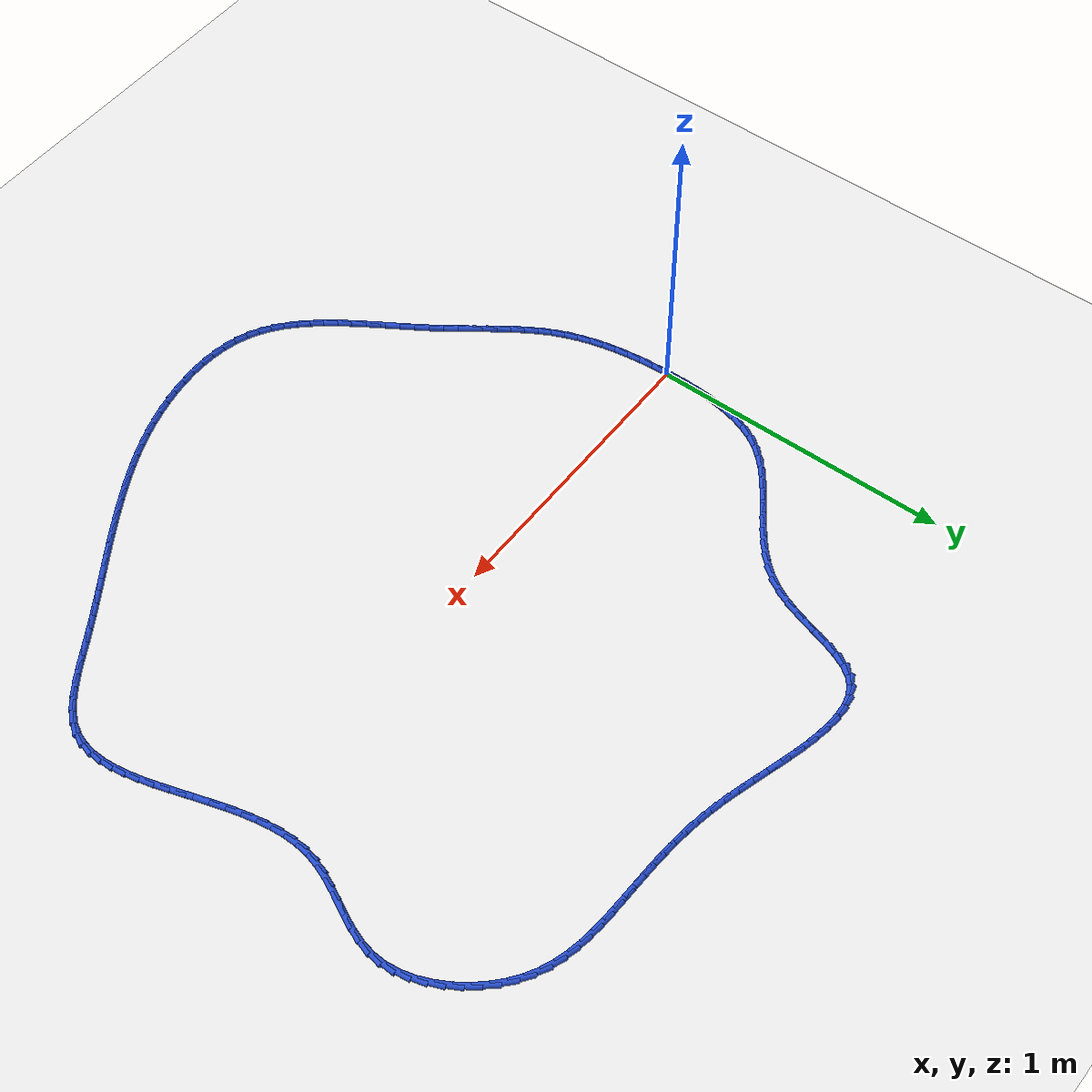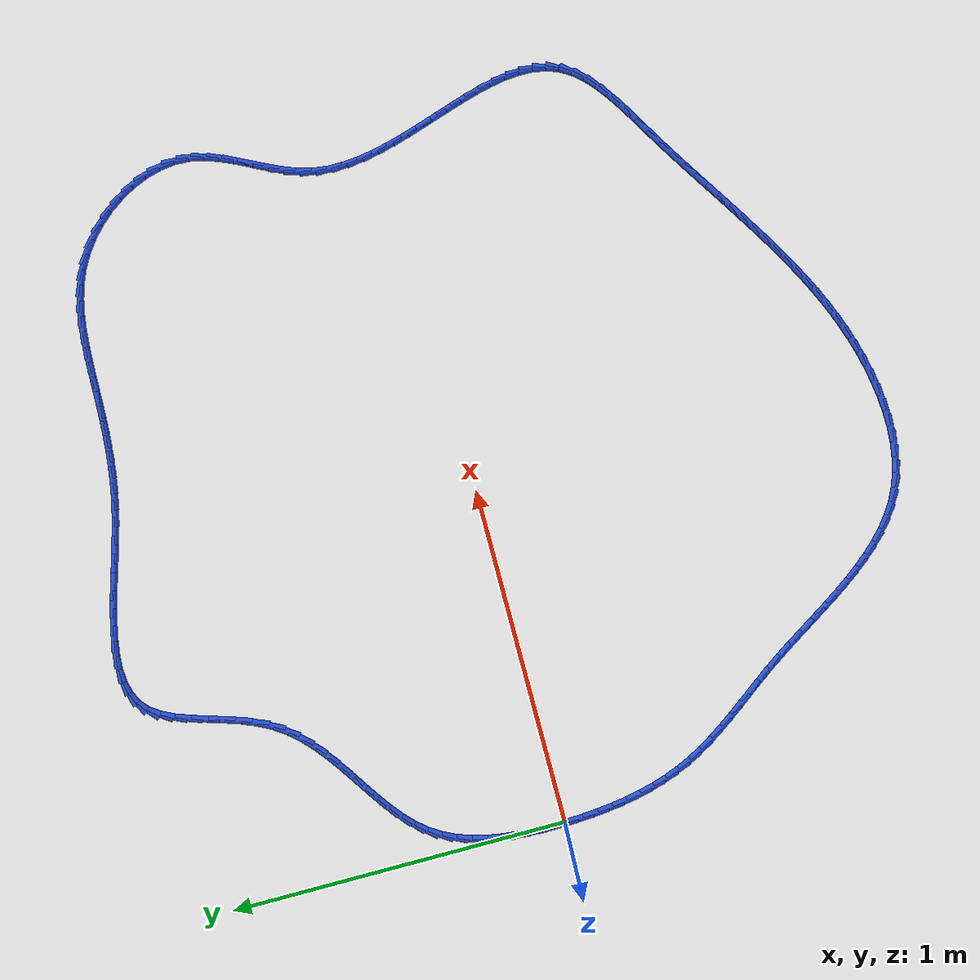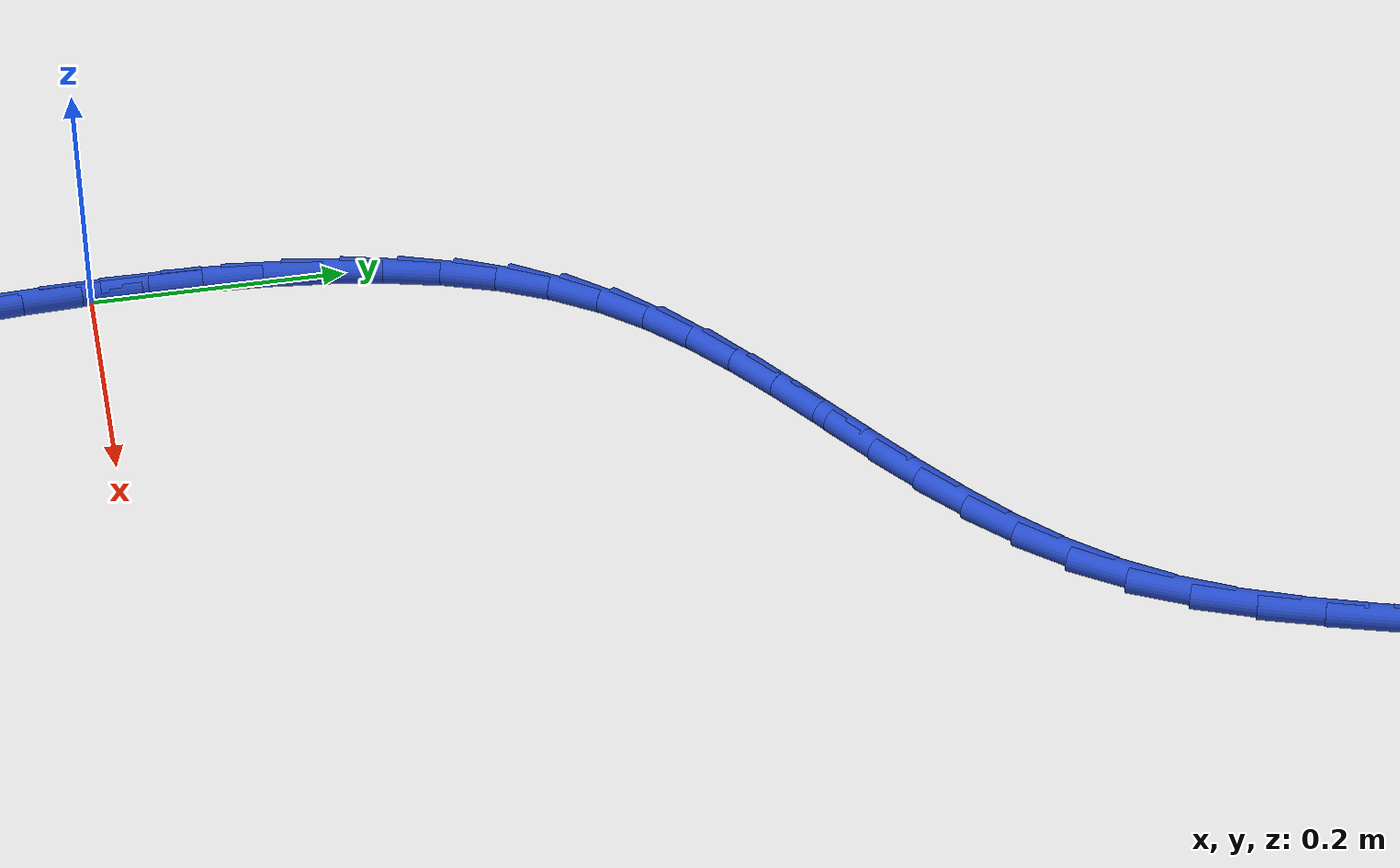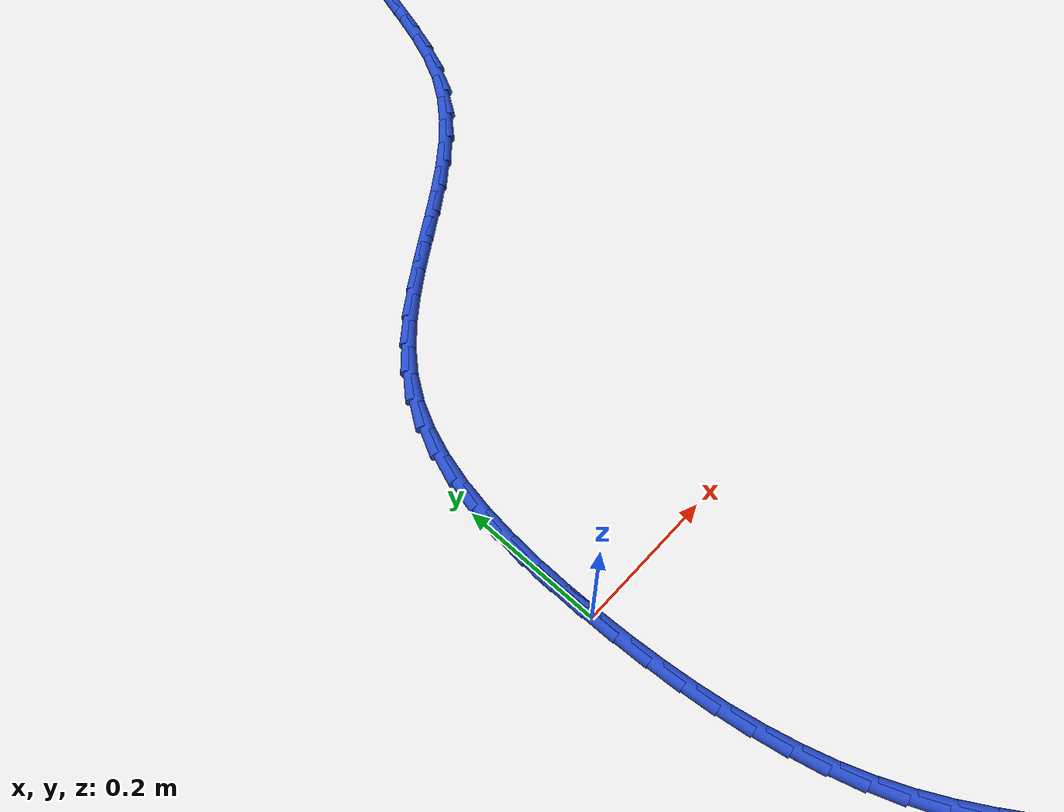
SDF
<sdf version="1.6">
 <world name="default">
  <light name="sun" type="directional">
   <pose>0 0 10 0 -0 0</pose>
   <diffuse>0.8 0.8 0.8 1</diffuse>
   <specular>0.2 0.2 0.2 1</specular>
   <attenuation>
    <range>1000</range>
    <constant>0.9</constant>
    <linear>0.01</linear>
    <quadratic>0.001</quadratic>
   </attenuation>
   <direction>-0.5 0.1 -0.9</direction>
  </light>
  <model name="ground_plane">
   <static>1</static>
   <link name="link">
    <collision name="collision">
     <geometry><plane><normal>0 0 1</normal><size>100 100</size></plane></geometry>
     <surface><friction><ode><mu>100</mu><mu2>50</mu2></ode></friction></surface>
    </collision>
    <visual name="visual">
     <cast_shadows>0</cast_shadows>
     <geometry><plane><normal>0 0 1</normal><size>100 100</size></plane></geometry>
     <material>
      <script><uri>file://media/materials/scripts/gazebo.material</uri><name>Gazebo/WhiteGlow</name></script>
     </material>
    </visual>
   </link>
  </model>
  <gravity>0 0 -9.8</gravity>
  <magnetic_field>6e-06 2.3e-05 -4.2e-05</magnetic_field>
  <atmosphere type="adiabatic"/>
  <physics name="default_physics" default="0" type="ode">
   <max_step_size>0.001</max_step_size>
   <real_time_factor>1</real_time_factor>
   <real_time_update_rate>1000</real_time_update_rate>
  </physics>
  <scene><ambient>0.4 0.4 0.4 1</ambient><background>0.7 0.7 0.7 1</background><shadows>1</shadows></scene>
  <spherical_coordinates>
   <surface_model>EARTH_WGS84</surface_model>
   <latitude_deg>0</latitude_deg>
   <longitude_deg>0</longitude_deg>
   <elevation>0</elevation>
   <heading_deg>0</heading_deg>
  </spherical_coordinates>
  <model name="line">
   <link name="link_0">
    <pose>-3.599551212651875e-17 5.551115123125783e-17 0.01 0 1.57 -1.554165532073075</pose>
    <collision name="collision">
     <geometry><cylinder><radius>0.01</radius><length>0.08</length></cylinder></geometry>
    </collision>
    <visual name="visual">
     <material>
      <script><name>Gazebo/Blue</name><uri>file://media/materials/scripts/gazebo.material</uri></script>
     </material>
     <geometry><cylinder><radius>0.01</radius><length>0.08</length></cylinder></geometry>
    </visual>
   </link>
   <link name="link_1">
    <pose>-0.0007946696506222375 0.047778617825266025 0.01 0 1.57 1.5540710812353986</pose>
    <collision name="collision">
     <geometry><cylinder><radius>0.01</radius><length>0.08</length></cylinder></geometry>
    </collision>
    <visual name="visual">
     <material>
      <script><name>Gazebo/Blue</name><uri>file://media/materials/scripts/gazebo.material</uri></script>
     </material>
     <geometry><cylinder><radius>0.01</radius><length>0.08</length></cylinder></geometry>
    </visual>
   </link>
   <link name="link_2">
    <pose>5.6341803319641176e-06 0.09562420566400855 0.01 0 1.57 1.511817530922678</pose>
    <collision name="collision">
     <geometry><cylinder><radius>0.01</radius><length>0.08</length></cylinder></geometry>
    </collision>
    <visual name="visual">
     <material>
      <script><name>Gazebo/Blue</name><uri>file://media/materials/scripts/gazebo.material</uri></script>
     </material>
     <geometry><cylinder><radius>0.01</radius><length>0.08</length></cylinder></geometry>
    </visual>
   </link>
   <link name="link_3">
    <pose>0.0028078790432107498 0.14308185321949368 0.01 0 1.57 1.4594667388106581</pose>
    <collision name="collision">
     <geometry><cylinder><radius>0.01</radius><length>0.08</length></cylinder></geometry>
    </collision>
    <visual name="visual">
     <material>
      <script><name>Gazebo/Blue</name><uri>file://media/materials/scripts/gazebo.material</uri></script>
     </material>
     <geometry><cylinder><radius>0.01</radius><length>0.08</length></cylinder></geometry>
    </visual>
   </link>
   <link name="link_4">
    <pose>0.008019032488362287 0.1896966501949873 0.01 0 1.57 1.3954842118591233</pose>
    <collision name="collision">
     <geometry><cylinder><radius>0.01</radius><length>0.08</length></cylinder></geometry>
    </collision>
    <visual name="visual">
     <material>
      <script><name>Gazebo/Blue</name><uri>file://media/materials/scripts/gazebo.material</uri></script>
     </material>
     <geometry><cylinder><radius>0.01</radius><length>0.08</length></cylinder></geometry>
    </visual>
   </link>
   <link name="link_5">
    <pose>0.016046062066134757 0.2350136862937556 0.01 0 1.57 1.318081584100216</pose>
    <collision name="collision">
     <geometry><cylinder><radius>0.01</radius><length>0.08</length></cylinder></geometry>
    </collision>
    <visual name="visual">
     <material>
      <script><name>Gazebo/Blue</name><uri>file://media/materials/scripts/gazebo.material</uri></script>
     </material>
     <geometry><cylinder><radius>0.01</radius><length>0.08</length></cylinder></geometry>
    </visual>
   </link>
   <link name="link_6">
    <pose>0.027295935326876346 0.27857805121906454 0.01 0 1.57 1.225428219969768</pose>
    <collision name="collision">
     <geometry><cylinder><radius>0.01</radius><length>0.08</length></cylinder></geometry>
    </collision>
    <visual name="visual">
     <material>
      <script><name>Gazebo/Blue</name><uri>file://media/materials/scripts/gazebo.material</uri></script>
     </material>
     <geometry><cylinder><radius>0.01</radius><length>0.08</length></cylinder></geometry>
    </visual>
   </link>
   <link name="link_7">
    <pose>0.04217561982093522 0.3199348346741801 0.01 0 1.57 1.1160926121666561</pose>
    <collision name="collision">
     <geometry><cylinder><radius>0.01</radius><length>0.08</length></cylinder></geometry>
    </collision>
    <visual name="visual">
     <material>
      <script><name>Gazebo/Blue</name><uri>file://media/materials/scripts/gazebo.material</uri></script>
     </material>
     <geometry><cylinder><radius>0.01</radius><length>0.08</length></cylinder></geometry>
    </visual>
   </link>
   <link name="link_8">
    <pose>0.061092083098659544 0.3586291263623683 0.01 0 1.57 0.9900174815071603</pose>
    <collision name="collision">
     <geometry><cylinder><radius>0.01</radius><length>0.08</length></cylinder></geometry>
    </collision>
    <visual name="visual">
     <material>
      <script><name>Gazebo/Blue</name><uri>file://media/materials/scripts/gazebo.material</uri></script>
     </material>
     <geometry><cylinder><radius>0.01</radius><length>0.08</length></cylinder></geometry>
    </visual>
   </link>
   <link name="link_9">
    <pose>0.08444497967276297 0.39421274776279663 0.01 0 1.57 0.8628762840987558</pose>
    <collision name="collision">
     <geometry><cylinder><radius>0.01</radius><length>0.08</length></cylinder></geometry>
    </collision>
    <visual name="visual">
     <material>
      <script><name>Gazebo/Blue</name><uri>file://media/materials/scripts/gazebo.material</uri></script>
     </material>
     <geometry><cylinder><radius>0.01</radius><length>0.08</length></cylinder></geometry>
    </visual>
   </link>
   <link name="link_10">
    <pose>0.11219859615573193 0.4266382839340592 0.01 0 1.57 0.7591932630883791</pose>
    <collision name="collision">
     <geometry><cylinder><radius>0.01</radius><length>0.08</length></cylinder></geometry>
    </collision>
    <visual name="visual">
     <material>
      <script><name>Gazebo/Blue</name><uri>file://media/materials/scripts/gazebo.material</uri></script>
     </material>
     <geometry><cylinder><radius>0.01</radius><length>0.08</length></cylinder></geometry>
    </visual>
   </link>
   <link name="link_11">
    <pose>0.14364435488279684 0.456477702980863 0.01 0 1.57 0.6814635301888626</pose>
    <collision name="collision">
     <geometry><cylinder><radius>0.01</radius><length>0.08</length></cylinder></geometry>
    </collision>
    <visual name="visual">
     <material>
      <script><name>Gazebo/Blue</name><uri>file://media/materials/scripts/gazebo.material</uri></script>
     </material>
     <geometry><cylinder><radius>0.01</radius><length>0.08</length></cylinder></geometry>
    </visual>
   </link>
   <link name="link_12">
    <pose>0.17801602539683592 0.4843560433868167 0.01 0 1.57 0.6283314219236602</pose>
    <collision name="collision">
     <geometry><cylinder><radius>0.01</radius><length>0.08</length></cylinder></geometry>
    </collision>
    <visual name="visual">
     <material>
      <script><name>Gazebo/Blue</name><uri>file://media/materials/scripts/gazebo.material</uri></script>
     </material>
     <geometry><cylinder><radius>0.01</radius><length>0.08</length></cylinder></geometry>
    </visual>
   </link>
   <link name="link_13">
    <pose>0.21454737724072706 0.5108983436355297 0.01 0 1.57 0.597941348197868</pose>
    <collision name="collision">
     <geometry><cylinder><radius>0.01</radius><length>0.08</length></cylinder></geometry>
    </collision>
    <visual name="visual">
     <material>
      <script><name>Gazebo/Blue</name><uri>file://media/materials/scripts/gazebo.material</uri></script>
     </material>
     <geometry><cylinder><radius>0.01</radius><length>0.08</length></cylinder></geometry>
    </visual>
   </link>
   <link name="link_14">
    <pose>0.2524721799573486 0.5367296422106106 0.01 0 1.57 0.5887920886620652</pose>
    <collision name="collision">
     <geometry><cylinder><radius>0.01</radius><length>0.08</length></cylinder></geometry>
    </collision>
    <visual name="visual">
     <material>
      <script><name>Gazebo/Blue</name><uri>file://media/materials/scripts/gazebo.material</uri></script>
     </material>
     <geometry><cylinder><radius>0.01</radius><length>0.08</length></cylinder></geometry>
    </visual>
   </link>
   <link name="link_15">
    <pose>0.29102420308957866 0.5624749775956689 0.01 0 1.57 0.6000825337693062</pose>
    <collision name="collision">
     <geometry><cylinder><radius>0.01</radius><length>0.08</length></cylinder></geometry>
    </collision>
    <visual name="visual">
     <material>
      <script><name>Gazebo/Blue</name><uri>file://media/materials/scripts/gazebo.material</uri></script>
     </material>
     <geometry><cylinder><radius>0.01</radius><length>0.08</length></cylinder></geometry>
    </visual>
   </link>
   <link name="link_16">
    <pose>0.3294372161802952 0.5887593882743134 0.01 0 1.57 0.631756837964478</pose>
    <collision name="collision">
     <geometry><cylinder><radius>0.01</radius><length>0.08</length></cylinder></geometry>
    </collision>
    <visual name="visual">
     <material>
      <script><name>Gazebo/Blue</name><uri>file://media/materials/scripts/gazebo.material</uri></script>
     </material>
     <geometry><cylinder><radius>0.01</radius><length>0.08</length></cylinder></geometry>
    </visual>
   </link>
   <link name="link_17">
    <pose>0.36694498877237663 0.6162079127301532 0.01 0 1.57 0.6843416865430514</pose>
    <collision name="collision">
     <geometry><cylinder><radius>0.01</radius><length>0.08</length></cylinder></geometry>
    </collision>
    <visual name="visual">
     <material>
      <script><name>Gazebo/Blue</name><uri>file://media/materials/scripts/gazebo.material</uri></script>
     </material>
     <geometry><cylinder><radius>0.01</radius><length>0.08</length></cylinder></geometry>
    </visual>
   </link>
   <link name="link_18">
    <pose>0.4027812904087007 0.6454455894467973 0.01 0 1.57 0.758552651109735</pose>
    <collision name="collision">
     <geometry><cylinder><radius>0.01</radius><length>0.08</length></cylinder></geometry>
    </collision>
    <visual name="visual">
     <material>
      <script><name>Gazebo/Blue</name><uri>file://media/materials/scripts/gazebo.material</uri></script>
     </material>
     <geometry><cylinder><radius>0.01</radius><length>0.08</length></cylinder></geometry>
    </visual>
   </link>
   <link name="link_19">
    <pose>0.4361798906321459 0.6770974569078549 0.01 0 1.57 0.8545851642665314</pose>
    <collision name="collision">
     <geometry><cylinder><radius>0.01</radius><length>0.08</length></cylinder></geometry>
    </collision>
    <visual name="visual">
     <material>
      <script><name>Gazebo/Blue</name><uri>file://media/materials/scripts/gazebo.material</uri></script>
     </material>
     <geometry><cylinder><radius>0.01</radius><length>0.08</length></cylinder></geometry>
    </visual>
   </link>
   <link name="link_20">
    <pose>0.4663745589855899 0.7117885535969348 0.01 0 1.57 0.9710771711306027</pose>
    <collision name="collision">
     <geometry><cylinder><radius>0.01</radius><length>0.08</length></cylinder></geometry>
    </collision>
    <visual name="visual">
     <material>
      <script><name>Gazebo/Blue</name><uri>file://media/materials/scripts/gazebo.material</uri></script>
     </material>
     <geometry><cylinder><radius>0.01</radius><length>0.08</length></cylinder></geometry>
    </visual>
   </link>
   <link name="link_21">
    <pose>0.4925990650119112 0.7501439179976461 0.01 0 1.57 1.097140017977338</pose>
    <collision name="collision">
     <geometry><cylinder><radius>0.01</radius><length>0.08</length></cylinder></geometry>
    </collision>
    <visual name="visual">
     <material>
      <script><name>Gazebo/Blue</name><uri>file://media/materials/scripts/gazebo.material</uri></script>
     </material>
     <geometry><cylinder><radius>0.01</radius><length>0.08</length></cylinder></geometry>
    </visual>
   </link>
   <link name="link_22">
    <pose>0.5143255672917966 0.7925309546713006 0.01 0 1.57 1.1927491478610073</pose>
    <collision name="collision">
     <geometry><cylinder><radius>0.01</radius><length>0.08</length></cylinder></geometry>
    </collision>
    <visual name="visual">
     <material>
      <script><name>Gazebo/Blue</name><uri>file://media/materials/scripts/gazebo.material</uri></script>
     </material>
     <geometry><cylinder><radius>0.01</radius><length>0.08</length></cylinder></geometry>
    </visual>
   </link>
   <link name="link_23">
    <pose>0.532341952472305 0.8378951228350259 0.01 0 1.57 1.2500849354145764</pose>
    <collision name="collision">
     <geometry><cylinder><radius>0.01</radius><length>0.08</length></cylinder></geometry>
    </collision>
    <visual name="visual">
     <material>
      <script><name>Gazebo/Blue</name><uri>file://media/materials/scripts/gazebo.material</uri></script>
     </material>
     <geometry><cylinder><radius>0.01</radius><length>0.08</length></cylinder></geometry>
    </visual>
   </link>
   <link name="link_24">
    <pose>0.5478875572504575 0.8846939865906275 0.01 0 1.57 1.2733111604714364</pose>
    <collision name="collision">
     <geometry><cylinder><radius>0.01</radius><length>0.08</length></cylinder></geometry>
    </collision>
    <visual name="visual">
     <material>
      <script><name>Gazebo/Blue</name><uri>file://media/materials/scripts/gazebo.material</uri></script>
     </material>
     <geometry><cylinder><radius>0.01</radius><length>0.08</length></cylinder></geometry>
    </visual>
   </link>
   <link name="link_25">
    <pose>0.5622021235116125 0.9313846721411653 0.01 0 1.57 1.2628952254583958</pose>
    <collision name="collision">
     <geometry><cylinder><radius>0.01</radius><length>0.08</length></cylinder></geometry>
    </collision>
    <visual name="visual">
     <material>
      <script><name>Gazebo/Blue</name><uri>file://media/materials/scripts/gazebo.material</uri></script>
     </material>
     <geometry><cylinder><radius>0.01</radius><length>0.08</length></cylinder></geometry>
    </visual>
   </link>
   <link name="link_26">
    <pose>0.576525393141129 0.9764243056896992 0.01 0 1.57 1.2145510840634388</pose>
    <collision name="collision">
     <geometry><cylinder><radius>0.01</radius><length>0.08</length></cylinder></geometry>
    </collision>
    <visual name="visual">
     <material>
      <script><name>Gazebo/Blue</name><uri>file://media/materials/scripts/gazebo.material</uri></script>
     </material>
     <geometry><cylinder><radius>0.01</radius><length>0.08</length></cylinder></geometry>
    </visual>
   </link>
   <link name="link_27">
    <pose>0.5920971080243657 1.0182700134392892 0.01 0 1.57 1.1178670824165902</pose>
    <collision name="collision">
     <geometry><cylinder><radius>0.01</radius><length>0.08</length></cylinder></geometry>
    </collision>
    <visual name="visual">
     <material>
      <script><name>Gazebo/Blue</name><uri>file://media/materials/scripts/gazebo.material</uri></script>
     </material>
     <geometry><cylinder><radius>0.01</radius><length>0.08</length></cylinder></geometry>
    </visual>
   </link>
   <link name="link_28">
    <pose>0.6101570100466811 1.0553789215929952 0.01 0 1.57 0.9555703170470435</pose>
    <collision name="collision">
     <geometry><cylinder><radius>0.01</radius><length>0.08</length></cylinder></geometry>
    </collision>
    <visual name="visual">
     <material>
      <script><name>Gazebo/Blue</name><uri>file://media/materials/scripts/gazebo.material</uri></script>
     </material>
     <geometry><cylinder><radius>0.01</radius><length>0.08</length></cylinder></geometry>
    </visual>
   </link>
   <link name="link_29">
    <pose>0.6319448410934337 1.0862081563538768 0.01 0 1.57 0.7150581808413605</pose>
    <collision name="collision">
     <geometry><cylinder><radius>0.01</radius><length>0.08</length></cylinder></geometry>
    </collision>
    <visual name="visual">
     <material>
      <script><name>Gazebo/Blue</name><uri>file://media/materials/scripts/gazebo.material</uri></script>
     </material>
     <geometry><cylinder><radius>0.01</radius><length>0.08</length></cylinder></geometry>
    </visual>
   </link>
   <link name="link_30">
    <pose>0.6585974692006238 1.1093522926734498 0.01 0 1.57 0.45520966451683714</pose>
    <collision name="collision">
     <geometry><cylinder><radius>0.01</radius><length>0.08</length></cylinder></geometry>
    </collision>
    <visual name="visual">
     <material>
      <script><name>Gazebo/Blue</name><uri>file://media/materials/scripts/gazebo.material</uri></script>
     </material>
     <geometry><cylinder><radius>0.01</radius><length>0.08</length></cylinder></geometry>
    </visual>
   </link>
   <link name="link_31">
    <pose>0.6901942648032124 1.1248188177512326 0.01 0 1.57 0.23521795588506128</pose>
    <collision name="collision">
     <geometry><cylinder><radius>0.01</radius><length>0.08</length></cylinder></geometry>
    </collision>
    <visual name="visual">
     <material>
      <script><name>Gazebo/Blue</name><uri>file://media/materials/scripts/gazebo.material</uri></script>
     </material>
     <geometry><cylinder><radius>0.01</radius><length>0.08</length></cylinder></geometry>
    </visual>
   </link>
   <link name="link_32">
    <pose>0.7261927878281897 1.1334460137519367 0.01 0 1.57 0.06607158520097124</pose>
    <collision name="collision">
     <geometry><cylinder><radius>0.01</radius><length>0.08</length></cylinder></geometry>
    </collision>
    <visual name="visual">
     <material>
      <script><name>Gazebo/Blue</name><uri>file://media/materials/scripts/gazebo.material</uri></script>
     </material>
     <geometry><cylinder><radius>0.01</radius><length>0.08</length></cylinder></geometry>
    </visual>
   </link>
   <link name="link_33">
    <pose>0.7660426407341805 1.1360827947362753 0.01 0 1.57 -0.057980696551498186</pose>
    <collision name="collision">
     <geometry><cylinder><radius>0.01</radius><length>0.08</length></cylinder></geometry>
    </collision>
    <visual name="visual">
     <material>
      <script><name>Gazebo/Blue</name><uri>file://media/materials/scripts/gazebo.material</uri></script>
     </material>
     <geometry><cylinder><radius>0.01</radius><length>0.08</length></cylinder></geometry>
    </visual>
   </link>
   <link name="link_34">
    <pose>0.8091934259798103 1.1335780747649624 0.01 0 1.57 -0.14701677366296806</pose>
    <collision name="collision">
     <geometry><cylinder><radius>0.01</radius><length>0.08</length></cylinder></geometry>
    </collision>
    <visual name="visual">
     <material>
      <script><name>Gazebo/Blue</name><uri>file://media/materials/scripts/gazebo.material</uri></script>
     </material>
     <geometry><cylinder><radius>0.01</radius><length>0.08</length></cylinder></geometry>
    </visual>
   </link>
   <link name="link_35">
    <pose>0.855094746023704 1.126780767898712 0.01 0 1.57 -0.20977164841910786</pose>
    <collision name="collision">
     <geometry><cylinder><radius>0.01</radius><length>0.08</length></cylinder></geometry>
    </collision>
    <visual name="visual">
     <material>
      <script><name>Gazebo/Blue</name><uri>file://media/materials/scripts/gazebo.material</uri></script>
     </material>
     <geometry><cylinder><radius>0.01</radius><length>0.08</length></cylinder></geometry>
    </visual>
   </link>
   <link name="link_36">
    <pose>0.9031962033244869 1.1165397881982373 0.01 0 1.57 -0.2524924611247231</pose>
    <collision name="collision">
     <geometry><cylinder><radius>0.01</radius><length>0.08</length></cylinder></geometry>
    </collision>
    <visual name="visual">
     <material>
      <script><name>Gazebo/Blue</name><uri>file://media/materials/scripts/gazebo.material</uri></script>
     </material>
     <geometry><cylinder><radius>0.01</radius><length>0.08</length></cylinder></geometry>
    </visual>
   </link>
   <link name="link_37">
    <pose>0.9529474003407836 1.1037040497242516 0.01 0 1.57 -0.27926041604706453</pose>
    <collision name="collision">
     <geometry><cylinder><radius>0.01</radius><length>0.08</length></cylinder></geometry>
    </collision>
    <visual name="visual">
     <material>
      <script><name>Gazebo/Blue</name><uri>file://media/materials/scripts/gazebo.material</uri></script>
     </material>
     <geometry><cylinder><radius>0.01</radius><length>0.08</length></cylinder></geometry>
    </visual>
   </link>
   <link name="link_38">
    <pose>1.00379793953122 1.0891224665374692 0.01 0 1.57 -0.292503644766396</pose>
    <collision name="collision">
     <geometry><cylinder><radius>0.01</radius><length>0.08</length></cylinder></geometry>
    </collision>
    <visual name="visual">
     <material>
      <script><name>Gazebo/Blue</name><uri>file://media/materials/scripts/gazebo.material</uri></script>
     </material>
     <geometry><cylinder><radius>0.01</radius><length>0.08</length></cylinder></geometry>
    </visual>
   </link>
   <link name="link_39">
    <pose>1.0551974233544206 1.0736439526986035 0.01 0 1.57 -0.2933677593075031</pose>
    <collision name="collision">
     <geometry><cylinder><radius>0.01</radius><length>0.08</length></cylinder></geometry>
    </collision>
    <visual name="visual">
     <material>
      <script><name>Gazebo/Blue</name><uri>file://media/materials/scripts/gazebo.material</uri></script>
     </material>
     <geometry><cylinder><radius>0.01</radius><length>0.08</length></cylinder></geometry>
    </visual>
   </link>
   <link name="link_40">
    <pose>1.1065954542690106 1.058117422268368 0.01 0 1.57 -0.28189892076825024</pose>
    <collision name="collision">
     <geometry><cylinder><radius>0.01</radius><length>0.08</length></cylinder></geometry>
    </collision>
    <visual name="visual">
     <material>
      <script><name>Gazebo/Blue</name><uri>file://media/materials/scripts/gazebo.material</uri></script>
     </material>
     <geometry><cylinder><radius>0.01</radius><length>0.08</length></cylinder></geometry>
    </visual>
   </link>
   <link name="link_41">
    <pose>1.1574416347336154 1.0433917893074762 0.01 0 1.57 -0.25704756320887173</pose>
    <collision name="collision">
     <geometry><cylinder><radius>0.01</radius><length>0.08</length></cylinder></geometry>
    </collision>
    <visual name="visual">
     <material>
      <script><name>Gazebo/Blue</name><uri>file://media/materials/scripts/gazebo.material</uri></script>
     </material>
     <geometry><cylinder><radius>0.01</radius><length>0.08</length></cylinder></geometry>
    </visual>
   </link>
   <link name="link_42">
    <pose>1.2071855672068597 1.0303159678766423 0.01 0 1.57 -0.2188253265229126</pose>
    <collision name="collision">
     <geometry><cylinder><radius>0.01</radius><length>0.08</length></cylinder></geometry>
    </collision>
    <visual name="visual">
     <material>
      <script><name>Gazebo/Blue</name><uri>file://media/materials/scripts/gazebo.material</uri></script>
     </material>
     <geometry><cylinder><radius>0.01</radius><length>0.08</length></cylinder></geometry>
    </visual>
   </link>
   <link name="link_43">
    <pose>1.2553755473382653 1.0195991750005597 0.01 0 1.57 -0.17815641731119658</pose>
    <collision name="collision">
     <geometry><cylinder><radius>0.01</radius><length>0.08</length></cylinder></geometry>
    </collision>
    <visual name="visual">
     <material>
      <script><name>Gazebo/Blue</name><uri>file://media/materials/scripts/gazebo.material</uri></script>
     </material>
     <geometry><cylinder><radius>0.01</radius><length>0.08</length></cylinder></geometry>
    </visual>
   </link>
   <link name="link_44">
    <pose>1.3021003082455773 1.011185655857562 0.01 0 1.57 -0.1402155038241167</pose>
    <collision name="collision">
     <geometry><cylinder><radius>0.01</radius><length>0.08</length></cylinder></geometry>
    </collision>
    <visual name="visual">
     <material>
      <script><name>Gazebo/Blue</name><uri>file://media/materials/scripts/gazebo.material</uri></script>
     </material>
     <geometry><cylinder><radius>0.01</radius><length>0.08</length></cylinder></geometry>
    </visual>
   </link>
   <link name="link_45">
    <pose>1.3476326267440555 1.0047591476942048 0.01 0 1.57 -0.10620456201255747</pose>
    <collision name="collision">
     <geometry><cylinder><radius>0.01</radius><length>0.08</length></cylinder></geometry>
    </collision>
    <visual name="visual">
     <material>
      <script><name>Gazebo/Blue</name><uri>file://media/materials/scripts/gazebo.material</uri></script>
     </material>
     <geometry><cylinder><radius>0.01</radius><length>0.08</length></cylinder></geometry>
    </visual>
   </link>
   <link name="link_46">
    <pose>1.392245434185021 1.000003169016221 0.01 0 1.57 -0.07722213106971512</pose>
    <collision name="collision">
     <geometry><cylinder><radius>0.01</radius><length>0.08</length></cylinder></geometry>
    </collision>
    <visual name="visual">
     <material>
      <script><name>Gazebo/Blue</name><uri>file://media/materials/scripts/gazebo.material</uri></script>
     </material>
     <geometry><cylinder><radius>0.01</radius><length>0.08</length></cylinder></geometry>
    </visual>
   </link>
   <link name="link_47">
    <pose>1.4362116619197953 0.9966012383293449 0.01 0 1.57 -0.054184676900650694</pose>
    <collision name="collision">
     <geometry><cylinder><radius>0.01</radius><length>0.08</length></cylinder></geometry>
    </collision>
    <visual name="visual">
     <material>
      <script><name>Gazebo/Blue</name><uri>file://media/materials/scripts/gazebo.material</uri></script>
     </material>
     <geometry><cylinder><radius>0.01</radius><length>0.08</length></cylinder></geometry>
    </visual>
   </link>
   <link name="link_48">
    <pose>1.4798042412997012 0.9942368741393101 0.01 0 1.57 -0.03776563671387576</pose>
    <collision name="collision">
     <geometry><cylinder><radius>0.01</radius><length>0.08</length></cylinder></geometry>
    </collision>
    <visual name="visual">
     <material>
      <script><name>Gazebo/Blue</name><uri>file://media/materials/scripts/gazebo.material</uri></script>
     </material>
     <geometry><cylinder><radius>0.01</radius><length>0.08</length></cylinder></geometry>
    </visual>
   </link>
   <link name="link_49">
    <pose>1.5232961036760597 0.9925935949518494 0.01 0 1.57 -0.028360694953792568</pose>
    <collision name="collision">
     <geometry><cylinder><radius>0.01</radius><length>0.08</length></cylinder></geometry>
    </collision>
    <visual name="visual">
     <material>
      <script><name>Gazebo/Blue</name><uri>file://media/materials/scripts/gazebo.material</uri></script>
     </material>
     <geometry><cylinder><radius>0.01</radius><length>0.08</length></cylinder></geometry>
    </visual>
   </link>
   <link name="link_50">
    <pose>1.5669601804001925 0.991354919272697 0.01 0 1.57 -0.026078284051155576</pose>
    <collision name="collision">
     <geometry><cylinder><radius>0.01</radius><length>0.08</length></cylinder></geometry>
    </collision>
    <visual name="visual">
     <material>
      <script><name>Gazebo/Blue</name><uri>file://media/materials/scripts/gazebo.material</uri></script>
     </material>
     <geometry><cylinder><radius>0.01</radius><length>0.08</length></cylinder></geometry>
    </visual>
   </link>
   <link name="link_51">
    <pose>1.611069402823422 0.9902043656075862 0.01 0 1.57 -0.031574615075211684</pose>
    <collision name="collision">
     <geometry><cylinder><radius>0.01</radius><length>0.08</length></cylinder></geometry>
    </collision>
    <visual name="visual">
     <material>
      <script><name>Gazebo/Blue</name><uri>file://media/materials/scripts/gazebo.material</uri></script>
     </material>
     <geometry><cylinder><radius>0.01</radius><length>0.08</length></cylinder></geometry>
    </visual>
   </link>
   <link name="link_52">
    <pose>1.6558444053412997 0.9887901421338448 0.01 0 1.57 -0.050833337259269765</pose>
    <collision name="collision">
     <geometry><cylinder><radius>0.01</radius><length>0.08</length></cylinder></geometry>
    </collision>
    <visual name="visual">
     <material>
      <script><name>Gazebo/Blue</name><uri>file://media/materials/scripts/gazebo.material</uri></script>
     </material>
     <geometry><cylinder><radius>0.01</radius><length>0.08</length></cylinder></geometry>
    </visual>
   </link>
   <link name="link_53">
    <pose>1.701101673973311 0.9864875804975812 0.01 0 1.57 -0.0866874292920707</pose>
    <collision name="collision">
     <geometry><cylinder><radius>0.01</radius><length>0.08</length></cylinder></geometry>
    </collision>
    <visual name="visual">
     <material>
      <script><name>Gazebo/Blue</name><uri>file://media/materials/scripts/gazebo.material</uri></script>
     </material>
     <geometry><cylinder><radius>0.01</radius><length>0.08</length></cylinder></geometry>
    </visual>
   </link>
   <link name="link_54">
    <pose>1.7464694132903058 0.9825448867849904 0.01 0 1.57 -0.13954339726666562</pose>
    <collision name="collision">
     <geometry><cylinder><radius>0.01</radius><length>0.08</length></cylinder></geometry>
    </collision>
    <visual name="visual">
     <material>
      <script><name>Gazebo/Blue</name><uri>file://media/materials/scripts/gazebo.material</uri></script>
     </material>
     <geometry><cylinder><radius>0.01</radius><length>0.08</length></cylinder></geometry>
    </visual>
   </link>
   <link name="link_55">
    <pose>1.791574775514135 0.9762095565478149 0.01 0 1.57 -0.21004296401570954</pose>
    <collision name="collision">
     <geometry><cylinder><radius>0.01</radius><length>0.08</length></cylinder></geometry>
    </collision>
    <visual name="visual">
     <material>
      <script><name>Gazebo/Blue</name><uri>file://media/materials/scripts/gazebo.material</uri></script>
     </material>
     <geometry><cylinder><radius>0.01</radius><length>0.08</length></cylinder></geometry>
    </visual>
   </link>
   <link name="link_56">
    <pose>1.836044912866647 0.9667290853377959 0.01 0 1.57 -0.2986076709436819</pose>
    <collision name="collision">
     <geometry><cylinder><radius>0.01</radius><length>0.08</length></cylinder></geometry>
    </collision>
    <visual name="visual">
     <material>
      <script><name>Gazebo/Blue</name><uri>file://media/materials/scripts/gazebo.material</uri></script>
     </material>
     <geometry><cylinder><radius>0.01</radius><length>0.08</length></cylinder></geometry>
    </visual>
   </link>
   <link name="link_57">
    <pose>1.8795069775696918 0.9533509687066757 0.01 0 1.57 -0.4047610908728204</pose>
    <collision name="collision">
     <geometry><cylinder><radius>0.01</radius><length>0.08</length></cylinder></geometry>
    </collision>
    <visual name="visual">
     <material>
      <script><name>Gazebo/Blue</name><uri>file://media/materials/scripts/gazebo.material</uri></script>
     </material>
     <geometry><cylinder><radius>0.01</radius><length>0.08</length></cylinder></geometry>
    </visual>
   </link>
   <link name="link_58">
    <pose>1.9215881218451185 0.9353227022061963 0.01 0 1.57 -0.5256735733633165</pose>
    <collision name="collision">
     <geometry><cylinder><radius>0.01</radius><length>0.08</length></cylinder></geometry>
    </collision>
    <visual name="visual">
     <material>
      <script><name>Gazebo/Blue</name><uri>file://media/materials/scripts/gazebo.material</uri></script>
     </material>
     <geometry><cylinder><radius>0.01</radius><length>0.08</length></cylinder></geometry>
    </visual>
   </link>
   <link name="link_59">
    <pose>1.9619090576013651 0.9119317214395879 0.01 0 1.57 -0.6461622778222932</pose>
    <collision name="collision">
     <geometry><cylinder><radius>0.01</radius><length>0.08</length></cylinder></geometry>
    </collision>
    <visual name="visual">
     <material>
      <script><name>Gazebo/Blue</name><uri>file://media/materials/scripts/gazebo.material</uri></script>
     </material>
     <geometry><cylinder><radius>0.01</radius><length>0.08</length></cylinder></geometry>
    </visual>
   </link>
   <link name="link_60">
    <pose>1.9999673002758194 0.8832294734927572 0.01 0 1.57 -0.7575470924110673</pose>
    <collision name="collision">
     <geometry><cylinder><radius>0.01</radius><length>0.08</length></cylinder></geometry>
    </collision>
    <visual name="visual">
     <material>
      <script><name>Gazebo/Blue</name><uri>file://media/materials/scripts/gazebo.material</uri></script>
     </material>
     <geometry><cylinder><radius>0.01</radius><length>0.08</length></cylinder></geometry>
    </visual>
   </link>
   <link name="link_61">
    <pose>2.0351496081503644 0.8499542736538162 0.01 0 1.57 -0.8636997728776732</pose>
    <collision name="collision">
     <geometry><cylinder><radius>0.01</radius><length>0.08</length></cylinder></geometry>
    </collision>
    <visual name="visual">
     <material>
      <script><name>Gazebo/Blue</name><uri>file://media/materials/scripts/gazebo.material</uri></script>
     </material>
     <geometry><cylinder><radius>0.01</radius><length>0.08</length></cylinder></geometry>
    </visual>
   </link>
   <link name="link_62">
    <pose>2.0668387958957752 0.812868893789425 0.01 0 1.57 -0.9687189788338244</pose>
    <collision name="collision">
     <geometry><cylinder><radius>0.01</radius><length>0.08</length></cylinder></geometry>
    </collision>
    <visual name="visual">
     <material>
      <script><name>Gazebo/Blue</name><uri>file://media/materials/scripts/gazebo.material</uri></script>
     </material>
     <geometry><cylinder><radius>0.01</radius><length>0.08</length></cylinder></geometry>
    </visual>
   </link>
   <link name="link_63">
    <pose>2.0944176781828268 0.772736105766242 0.01 0 1.57 -1.0766495571068124</pose>
    <collision name="collision">
     <geometry><cylinder><radius>0.01</radius><length>0.08</length></cylinder></geometry>
    </collision>
    <visual name="visual">
     <material>
      <script><name>Gazebo/Blue</name><uri>file://media/materials/scripts/gazebo.material</uri></script>
     </material>
     <geometry><cylinder><radius>0.01</radius><length>0.08</length></cylinder></geometry>
    </visual>
   </link>
   <link name="link_64">
    <pose>2.117269069682293 0.7303186814509276 0.01 0 1.57 -1.1916444333201475</pose>
    <collision name="collision">
     <geometry><cylinder><radius>0.01</radius><length>0.08</length></cylinder></geometry>
    </collision>
    <visual name="visual">
     <material>
      <script><name>Gazebo/Blue</name><uri>file://media/materials/scripts/gazebo.material</uri></script>
     </material>
     <geometry><cylinder><radius>0.01</radius><length>0.08</length></cylinder></geometry>
    </visual>
   </link>
   <link name="link_65">
    <pose>2.13477578506495 0.6863793927101408 0.01 0 1.57 -1.3180367601791791</pose>
    <collision name="collision">
     <geometry><cylinder><radius>0.01</radius><length>0.08</length></cylinder></geometry>
    </collision>
    <visual name="visual">
     <material>
      <script><name>Gazebo/Blue</name><uri>file://media/materials/scripts/gazebo.material</uri></script>
     </material>
     <geometry><cylinder><radius>0.01</radius><length>0.08</length></cylinder></geometry>
    </visual>
   </link>
   <link name="link_66">
    <pose>2.146320639001571 0.6416810114105402 0.01 0 1.57 -1.4601450914535388</pose>
    <collision name="collision">
     <geometry><cylinder><radius>0.01</radius><length>0.08</length></cylinder></geometry>
    </collision>
    <visual name="visual">
     <material>
      <script><name>Gazebo/Blue</name><uri>file://media/materials/scripts/gazebo.material</uri></script>
     </material>
     <geometry><cylinder><radius>0.01</radius><length>0.08</length></cylinder></geometry>
    </visual>
   </link>
   <link name="link_67">
    <pose>2.151286446162932 0.5969863094187864 0.01 0 1.57 1.5202927509333584</pose>
    <collision name="collision">
     <geometry><cylinder><radius>0.01</radius><length>0.08</length></cylinder></geometry>
    </collision>
    <visual name="visual">
     <material>
      <script><name>Gazebo/Blue</name><uri>file://media/materials/scripts/gazebo.material</uri></script>
     </material>
     <geometry><cylinder><radius>0.01</radius><length>0.08</length></cylinder></geometry>
    </visual>
   </link>
   <link name="link_68">
    <pose>2.14906579100036 0.5530534433926741 0.01 0 1.57 1.3586519011553262</pose>
    <collision name="collision">
     <geometry><cylinder><radius>0.01</radius><length>0.08</length></cylinder></geometry>
    </collision>
    <visual name="visual">
     <material>
      <script><name>Gazebo/Blue</name><uri>file://media/materials/scripts/gazebo.material</uri></script>
     </material>
     <geometry><cylinder><radius>0.01</radius><length>0.08</length></cylinder></geometry>
    </visual>
   </link>
   <link name="link_69">
    <pose>2.139849465325234 0.5102634997310374 0.01 0 1.57 1.2346990748952713</pose>
    <collision name="collision">
     <geometry><cylinder><radius>0.01</radius><length>0.08</length></cylinder></geometry>
    </collision>
    <visual name="visual">
     <material>
      <script><name>Gazebo/Blue</name><uri>file://media/materials/scripts/gazebo.material</uri></script>
     </material>
     <geometry><cylinder><radius>0.01</radius><length>0.08</length></cylinder></geometry>
    </visual>
   </link>
   <link name="link_70">
    <pose>2.1252057978249317 0.4683468214136925 0.01 0 1.57 1.153054852317877</pose>
    <collision name="collision">
     <geometry><cylinder><radius>0.01</radius><length>0.08</length></cylinder></geometry>
    </collision>
    <visual name="visual">
     <material>
      <script><name>Gazebo/Blue</name><uri>file://media/materials/scripts/gazebo.material</uri></script>
     </material>
     <geometry><cylinder><radius>0.01</radius><length>0.08</length></cylinder></geometry>
    </visual>
   </link>
   <link name="link_71">
    <pose>2.1068396818772888 0.42696923875648796 0.01 0 1.57 1.1110941723923164</pose>
    <collision name="collision">
     <geometry><cylinder><radius>0.01</radius><length>0.08</length></cylinder></geometry>
    </collision>
    <visual name="visual">
     <material>
      <script><name>Gazebo/Blue</name><uri>file://media/materials/scripts/gazebo.material</uri></script>
     </material>
     <geometry><cylinder><radius>0.01</radius><length>0.08</length></cylinder></geometry>
    </visual>
   </link>
   <link name="link_72">
    <pose>2.086456010860141 0.38579658207527323 0.01 0 1.57 1.1062700644774541</pose>
    <collision name="collision">
     <geometry><cylinder><radius>0.01</radius><length>0.08</length></cylinder></geometry>
    </collision>
    <visual name="visual">
     <material>
      <script><name>Gazebo/Blue</name><uri>file://media/materials/scripts/gazebo.material</uri></script>
     </material>
     <geometry><cylinder><radius>0.01</radius><length>0.08</length></cylinder></geometry>
    </visual>
   </link>
   <link name="link_73">
    <pose>2.0657596781513248 0.3444946816858967 0.01 0 1.57 1.1378399097468377</pose>
    <collision name="collision">
     <geometry><cylinder><radius>0.01</radius><length>0.08</length></cylinder></geometry>
    </collision>
    <visual name="visual">
     <material>
      <script><name>Gazebo/Blue</name><uri>file://media/materials/scripts/gazebo.material</uri></script>
     </material>
     <geometry><cylinder><radius>0.01</radius><length>0.08</length></cylinder></geometry>
    </visual>
   </link>
   <link name="link_74">
    <pose>2.0464555771286745 0.30272936790420757 0.01 0 1.57 1.2069704560773555</pose>
    <collision name="collision">
     <geometry><cylinder><radius>0.01</radius><length>0.08</length></cylinder></geometry>
    </collision>
    <visual name="visual">
     <material>
      <script><name>Gazebo/Blue</name><uri>file://media/materials/scripts/gazebo.material</uri></script>
     </material>
     <geometry><cylinder><radius>0.01</radius><length>0.08</length></cylinder></geometry>
    </visual>
   </link>
   <link name="link_75">
    <pose>2.0302486011700265 0.2601664710460544 0.01 0 1.57 1.3154053156962984</pose>
    <collision name="collision">
     <geometry><cylinder><radius>0.01</radius><length>0.08</length></cylinder></geometry>
    </collision>
    <visual name="visual">
     <material>
      <script><name>Gazebo/Blue</name><uri>file://media/materials/scripts/gazebo.material</uri></script>
     </material>
     <geometry><cylinder><radius>0.01</radius><length>0.08</length></cylinder></geometry>
    </visual>
   </link>
   <link name="link_76">
    <pose>2.018840449403308 0.21647254513109843 0.01 0 1.57 1.4469641923259475</pose>
    <collision name="collision">
     <geometry><cylinder><radius>0.01</radius><length>0.08</length></cylinder></geometry>
    </collision>
    <visual name="visual">
     <material>
      <script><name>Gazebo/Blue</name><uri>file://media/materials/scripts/gazebo.material</uri></script>
     </material>
     <geometry><cylinder><radius>0.01</radius><length>0.08</length></cylinder></geometry>
    </visual>
   </link>
   <link name="link_77">
    <pose>2.013239188785338 0.17147129664407226 0.01 0 1.57 1.563382027461413</pose>
    <collision name="collision">
     <geometry><cylinder><radius>0.01</radius><length>0.08</length></cylinder></geometry>
    </collision>
    <visual name="visual">
     <material>
      <script><name>Gazebo/Blue</name><uri>file://media/materials/scripts/gazebo.material</uri></script>
     </material>
     <geometry><cylinder><radius>0.01</radius><length>0.08</length></cylinder></geometry>
    </visual>
   </link>
   <link name="link_78">
    <pose>2.0128971431816343 0.12533890831287417 0.01 0 1.57 -1.482637314583374</pose>
    <collision name="collision">
     <geometry><cylinder><radius>0.01</radius><length>0.08</length></cylinder></geometry>
    </collision>
    <visual name="visual">
     <material>
      <script><name>Gazebo/Blue</name><uri>file://media/materials/scripts/gazebo.material</uri></script>
     </material>
     <geometry><cylinder><radius>0.01</radius><length>0.08</length></cylinder></geometry>
    </visual>
   </link>
   <link name="link_79">
    <pose>2.017054864033257 0.07829954299078504 0.01 0 1.57 -1.40678263072887</pose>
    <collision name="collision">
     <geometry><cylinder><radius>0.01</radius><length>0.08</length></cylinder></geometry>
    </collision>
    <visual name="visual">
     <material>
      <script><name>Gazebo/Blue</name><uri>file://media/materials/scripts/gazebo.material</uri></script>
     </material>
     <geometry><cylinder><radius>0.01</radius><length>0.08</length></cylinder></geometry>
    </visual>
   </link>
   <link name="link_80">
    <pose>2.0249529027812616 0.03057736353108418 0.01 0 1.57 -1.3487269520165397</pose>
    <collision name="collision">
     <geometry><cylinder><radius>0.01</radius><length>0.08</length></cylinder></geometry>
    </collision>
    <visual name="visual">
     <material>
      <script><name>Gazebo/Blue</name><uri>file://media/materials/scripts/gazebo.material</uri></script>
     </material>
     <geometry><cylinder><radius>0.01</radius><length>0.08</length></cylinder></geometry>
    </visual>
   </link>
   <link name="link_81">
    <pose>2.035831810866708 -0.017603467212948684 0.01 0 1.57 -1.306541828671623</pose>
    <collision name="collision">
     <geometry><cylinder><radius>0.01</radius><length>0.08</length></cylinder></geometry>
    </collision>
    <visual name="visual">
     <material>
      <script><name>Gazebo/Blue</name><uri>file://media/materials/scripts/gazebo.material</uri></script>
     </material>
     <geometry><cylinder><radius>0.01</radius><length>0.08</length></cylinder></geometry>
    </visual>
   </link>
   <link name="link_82">
    <pose>2.048932139730655 -0.06601878638803448 0.01 0 1.57 -1.2786840140187428</pose>
    <collision name="collision">
     <geometry><cylinder><radius>0.01</radius><length>0.08</length></cylinder></geometry>
    </collision>
    <visual name="visual">
     <material>
      <script><name>Gazebo/Blue</name><uri>file://media/materials/scripts/gazebo.material</uri></script>
     </material>
     <geometry><cylinder><radius>0.01</radius><length>0.08</length></cylinder></geometry>
    </visual>
   </link>
   <link name="link_83">
    <pose>2.0634944408141584 -0.11444443114089173 0.01 0 1.57 -1.2641623788773009</pose>
    <collision name="collision">
     <geometry><cylinder><radius>0.01</radius><length>0.08</length></cylinder></geometry>
    </collision>
    <visual name="visual">
     <material>
      <script><name>Gazebo/Blue</name><uri>file://media/materials/scripts/gazebo.material</uri></script>
     </material>
     <geometry><cylinder><radius>0.01</radius><length>0.08</length></cylinder></geometry>
    </visual>
   </link>
   <link name="link_84">
    <pose>2.0787592655582796 -0.16265623861824155 0.01 0 1.57 -1.2626077807521692</pose>
    <collision name="collision">
     <geometry><cylinder><radius>0.01</radius><length>0.08</length></cylinder></geometry>
    </collision>
    <visual name="visual">
     <material>
      <script><name>Gazebo/Blue</name><uri>file://media/materials/scripts/gazebo.material</uri></script>
     </material>
     <geometry><cylinder><radius>0.01</radius><length>0.08</length></cylinder></geometry>
    </visual>
   </link>
   <link name="link_85">
    <pose>2.093967165404075 -0.21043004596680398 0.01 0 1.57 -1.274322316343719</pose>
    <collision name="collision">
     <geometry><cylinder><radius>0.01</radius><length>0.08</length></cylinder></geometry>
    </collision>
    <visual name="visual">
     <material>
      <script><name>Gazebo/Blue</name><uri>file://media/materials/scripts/gazebo.material</uri></script>
     </material>
     <geometry><cylinder><radius>0.01</radius><length>0.08</length></cylinder></geometry>
    </visual>
   </link>
   <link name="link_86">
    <pose>2.1083586917926036 -0.2575416903332993 0.01 0 1.57 -1.30034484187188</pose>
    <collision name="collision">
     <geometry><cylinder><radius>0.01</radius><length>0.08</length></cylinder></geometry>
    </collision>
    <visual name="visual">
     <material>
      <script><name>Gazebo/Blue</name><uri>file://media/materials/scripts/gazebo.material</uri></script>
     </material>
     <geometry><cylinder><radius>0.01</radius><length>0.08</length></cylinder></geometry>
    </visual>
   </link>
   <link name="link_87">
    <pose>2.1211743961649225 -0.3037670088644485 0.01 0 1.57 -1.342539152986948</pose>
    <collision name="collision">
     <geometry><cylinder><radius>0.01</radius><length>0.08</length></cylinder></geometry>
    </collision>
    <visual name="visual">
     <material>
      <script><name>Gazebo/Blue</name><uri>file://media/materials/scripts/gazebo.material</uri></script>
     </material>
     <geometry><cylinder><radius>0.01</radius><length>0.08</length></cylinder></geometry>
    </visual>
   </link>
   <link name="link_88">
    <pose>2.1316548299620917 -0.3488818387069702 0.01 0 1.57 -1.4036699571492643</pose>
    <collision name="collision">
     <geometry><cylinder><radius>0.01</radius><length>0.08</length></cylinder></geometry>
    </collision>
    <visual name="visual">
     <material>
      <script><name>Gazebo/Blue</name><uri>file://media/materials/scripts/gazebo.material</uri></script>
     </material>
     <geometry><cylinder><radius>0.01</radius><length>0.08</length></cylinder></geometry>
    </visual>
   </link>
   <link name="link_89">
    <pose>2.1390405446251677 -0.3926620170075852 0.01 0 1.57 -1.4873469736714229</pose>
    <collision name="collision">
     <geometry><cylinder><radius>0.01</radius><length>0.08</length></cylinder></geometry>
    </collision>
    <visual name="visual">
     <material>
      <script><name>Gazebo/Blue</name><uri>file://media/materials/scripts/gazebo.material</uri></script>
     </material>
     <geometry><cylinder><radius>0.01</radius><length>0.08</length></cylinder></geometry>
    </visual>
   </link>
   <link name="link_90">
    <pose>2.1425720915952104 -0.43488338091301404 0.01 0 1.57 1.5440442423830665</pose>
    <collision name="collision">
     <geometry><cylinder><radius>0.01</radius><length>0.08</length></cylinder></geometry>
    </collision>
    <visual name="visual">
     <material>
      <script><name>Gazebo/Blue</name><uri>file://media/materials/scripts/gazebo.material</uri></script>
     </material>
     <geometry><cylinder><radius>0.01</radius><length>0.08</length></cylinder></geometry>
    </visual>
   </link>
   <link name="link_91">
    <pose>2.141490022313277 -0.47532176756997646 0.01 0 1.57 1.4043839194622698</pose>
    <collision name="collision">
     <geometry><cylinder><radius>0.01</radius><length>0.08</length></cylinder></geometry>
    </collision>
    <visual name="visual">
     <material>
      <script><name>Gazebo/Blue</name><uri>file://media/materials/scripts/gazebo.material</uri></script>
     </material>
     <geometry><cylinder><radius>0.01</radius><length>0.08</length></cylinder></geometry>
    </visual>
   </link>
   <link name="link_92">
    <pose>2.1350348882204258 -0.5137530141251936 0.01 0 1.57 1.236149125360986</pose>
    <collision name="collision">
     <geometry><cylinder><radius>0.01</radius><length>0.08</length></cylinder></geometry>
    </collision>
    <visual name="visual">
     <material>
      <script><name>Gazebo/Blue</name><uri>file://media/materials/scripts/gazebo.material</uri></script>
     </material>
     <geometry><cylinder><radius>0.01</radius><length>0.08</length></cylinder></geometry>
    </visual>
   </link>
   <link name="link_93">
    <pose>2.122447240757716 -0.5499529577253844 0.01 0 1.57 1.0479607116930774</pose>
    <collision name="collision">
     <geometry><cylinder><radius>0.01</radius><length>0.08</length></cylinder></geometry>
    </collision>
    <visual name="visual">
     <material>
      <script><name>Gazebo/Blue</name><uri>file://media/materials/scripts/gazebo.material</uri></script>
     </material>
     <geometry><cylinder><radius>0.01</radius><length>0.08</length></cylinder></geometry>
    </visual>
   </link>
   <link name="link_94">
    <pose>2.1029944278024404 -0.5837056791967781 0.01 0 1.57 0.8750167726461675</pose>
    <collision name="collision">
     <geometry><cylinder><radius>0.01</radius><length>0.08</length></cylinder></geometry>
    </collision>
    <visual name="visual">
     <material>
      <script><name>Gazebo/Blue</name><uri>file://media/materials/scripts/gazebo.material</uri></script>
     </material>
     <geometry><cylinder><radius>0.01</radius><length>0.08</length></cylinder></geometry>
    </visual>
   </link>
   <link name="link_95">
    <pose>2.07680920905832 -0.6150614954306259 0.01 0 1.57 0.7456910814754769</pose>
    <collision name="collision">
     <geometry><cylinder><radius>0.01</radius><length>0.08</length></cylinder></geometry>
    </collision>
    <visual name="visual">
     <material>
      <script><name>Gazebo/Blue</name><uri>file://media/materials/scripts/gazebo.material</uri></script>
     </material>
     <geometry><cylinder><radius>0.01</radius><length>0.08</length></cylinder></geometry>
    </visual>
   </link>
   <link name="link_96">
    <pose>2.045056019507198 -0.6443881088195568 0.01 0 1.57 0.6542539412834865</pose>
    <collision name="collision">
     <geometry><cylinder><radius>0.01</radius><length>0.08</length></cylinder></geometry>
    </collision>
    <visual name="visual">
     <material>
      <script><name>Gazebo/Blue</name><uri>file://media/materials/scripts/gazebo.material</uri></script>
     </material>
     <geometry><cylinder><radius>0.01</radius><length>0.08</length></cylinder></geometry>
    </visual>
   </link>
   <link name="link_97">
    <pose>2.0089596655055786 -0.6720717944596654 0.01 0 1.57 0.5929977746168692</pose>
    <collision name="collision">
     <geometry><cylinder><radius>0.01</radius><length>0.08</length></cylinder></geometry>
    </collision>
    <visual name="visual">
     <material>
      <script><name>Gazebo/Blue</name><uri>file://media/materials/scripts/gazebo.material</uri></script>
     </material>
     <geometry><cylinder><radius>0.01</radius><length>0.08</length></cylinder></geometry>
    </visual>
   </link>
   <link name="link_98">
    <pose>1.969744953409959 -0.6984988274470466 0.01 0 1.57 0.5562165821362881</pose>
    <collision name="collision">
     <geometry><cylinder><radius>0.01</radius><length>0.08</length></cylinder></geometry>
    </collision>
    <visual name="visual">
     <material>
      <script><name>Gazebo/Blue</name><uri>file://media/materials/scripts/gazebo.material</uri></script>
     </material>
     <geometry><cylinder><radius>0.01</radius><length>0.08</length></cylinder></geometry>
    </visual>
   </link>
   <link name="link_99">
    <pose>1.9286366895768419 -0.7240554828777959 0.01 0 1.57 0.5405312106064081</pose>
    <collision name="collision">
     <geometry><cylinder><radius>0.01</radius><length>0.08</length></cylinder></geometry>
    </collision>
    <visual name="visual">
     <material>
      <script><name>Gazebo/Blue</name><uri>file://media/materials/scripts/gazebo.material</uri></script>
     </material>
     <geometry><cylinder><radius>0.01</radius><length>0.08</length></cylinder></geometry>
    </visual>
   </link>
   <link name="link_100">
    <pose>1.8868596803627264 -0.7491280358480079 0.01 0 1.57 0.5440728545800273</pose>
    <collision name="collision">
     <geometry><cylinder><radius>0.01</radius><length>0.08</length></cylinder></geometry>
    </collision>
    <visual name="visual">
     <material>
      <script><name>Gazebo/Blue</name><uri>file://media/materials/scripts/gazebo.material</uri></script>
     </material>
     <geometry><cylinder><radius>0.01</radius><length>0.08</length></cylinder></geometry>
    </visual>
   </link>
   <link name="link_101">
    <pose>1.8455991161535914 -0.7740898313174609 0.01 0 1.57 0.555580553844442</pose>
    <collision name="collision">
     <geometry><cylinder><radius>0.01</radius><length>0.08</length></cylinder></geometry>
    </collision>
    <visual name="visual">
     <material>
      <script><name>Gazebo/Blue</name><uri>file://media/materials/scripts/gazebo.material</uri></script>
     </material>
     <geometry><cylinder><radius>0.01</radius><length>0.08</length></cylinder></geometry>
    </visual>
   </link>
   <link name="link_102">
    <pose>1.8053372635820897 -0.7990847890966379 0.01 0 1.57 0.5651399592220017</pose>
    <collision name="collision">
     <geometry><cylinder><radius>0.01</radius><length>0.08</length></cylinder></geometry>
    </collision>
    <visual name="visual">
     <material>
      <script><name>Gazebo/Blue</name><uri>file://media/materials/scripts/gazebo.material</uri></script>
     </material>
     <geometry><cylinder><radius>0.01</radius><length>0.08</length></cylinder></geometry>
    </visual>
   </link>
   <link name="link_103">
    <pose>1.7659527518113018 -0.8240598095953846 0.01 0 1.57 0.5722585470033482</pose>
    <collision name="collision">
     <geometry><cylinder><radius>0.01</radius><length>0.08</length></cylinder></geometry>
    </collision>
    <visual name="visual">
     <material>
      <script><name>Gazebo/Blue</name><uri>file://media/materials/scripts/gazebo.material</uri></script>
     </material>
     <geometry><cylinder><radius>0.01</radius><length>0.08</length></cylinder></geometry>
    </visual>
   </link>
   <link name="link_104">
    <pose>1.727304595740349 -0.8489553913834956 0.01 0 1.57 0.5767876548533839</pose>
    <collision name="collision">
     <geometry><cylinder><radius>0.01</radius><length>0.08</length></cylinder></geometry>
    </collision>
    <visual name="visual">
     <material>
      <script><name>Gazebo/Blue</name><uri>file://media/materials/scripts/gazebo.material</uri></script>
     </material>
     <geometry><cylinder><radius>0.01</radius><length>0.08</length></cylinder></geometry>
    </visual>
   </link>
   <link name="link_105">
    <pose>1.6892518102683503 -0.8737120330307628 0.01 0 1.57 0.5786014558013306</pose>
    <collision name="collision">
     <geometry><cylinder><radius>0.01</radius><length>0.08</length></cylinder></geometry>
    </collision>
    <visual name="visual">
     <material>
      <script><name>Gazebo/Blue</name><uri>file://media/materials/scripts/gazebo.material</uri></script>
     </material>
     <geometry><cylinder><radius>0.01</radius><length>0.08</length></cylinder></geometry>
    </visual>
   </link>
   <link name="link_106">
    <pose>1.6516534102944247 -0.8982702331069811 0.01 0 1.57 0.5775999212968783</pose>
    <collision name="collision">
     <geometry><cylinder><radius>0.01</radius><length>0.08</length></cylinder></geometry>
    </collision>
    <visual name="visual">
     <material>
      <script><name>Gazebo/Blue</name><uri>file://media/materials/scripts/gazebo.material</uri></script>
     </material>
     <geometry><cylinder><radius>0.01</radius><length>0.08</length></cylinder></geometry>
    </visual>
   </link>
   <link name="link_107">
    <pose>1.6143684107176945 -0.9225704901819428 0.01 0 1.57 0.5737117852068002</pose>
    <collision name="collision">
     <geometry><cylinder><radius>0.01</radius><length>0.08</length></cylinder></geometry>
    </collision>
    <visual name="visual">
     <material>
      <script><name>Gazebo/Blue</name><uri>file://media/materials/scripts/gazebo.material</uri></script>
     </material>
     <geometry><cylinder><radius>0.01</radius><length>0.08</length></cylinder></geometry>
    </visual>
   </link>
   <link name="link_108">
    <pose>1.577255826437278 -0.9465533028254411 0.01 0 1.57 0.5668975133222439</pose>
    <collision name="collision">
     <geometry><cylinder><radius>0.01</radius><length>0.08</length></cylinder></geometry>
    </collision>
    <visual name="visual">
     <material>
      <script><name>Gazebo/Blue</name><uri>file://media/materials/scripts/gazebo.material</uri></script>
     </material>
     <geometry><cylinder><radius>0.01</radius><length>0.08</length></cylinder></geometry>
    </visual>
   </link>
   <link name="link_109">
    <pose>1.5401746723522953 -0.97015916960727 0.01 0 1.57 0.5571522228902352</pose>
    <collision name="collision">
     <geometry><cylinder><radius>0.01</radius><length>0.08</length></cylinder></geometry>
    </collision>
    <visual name="visual">
     <material>
      <script><name>Gazebo/Blue</name><uri>file://media/materials/scripts/gazebo.material</uri></script>
     </material>
     <geometry><cylinder><radius>0.01</radius><length>0.08</length></cylinder></geometry>
    </visual>
   </link>
   <link name="link_110">
    <pose>1.5029839633618665 -0.9933285890972228 0.01 0 1.57 0.5445084188971039</pose>
    <collision name="collision">
     <geometry><cylinder><radius>0.01</radius><length>0.08</length></cylinder></geometry>
    </collision>
    <visual name="visual">
     <material>
      <script><name>Gazebo/Blue</name><uri>file://media/materials/scripts/gazebo.material</uri></script>
     </material>
     <geometry><cylinder><radius>0.01</radius><length>0.08</length></cylinder></geometry>
    </visual>
   </link>
   <link name="link_111">
    <pose>1.4655427143651105 -1.016002059865093 0.01 0 1.57 0.5290383277724462</pose>
    <collision name="collision">
     <geometry><cylinder><radius>0.01</radius><length>0.08</length></cylinder></geometry>
    </collision>
    <visual name="visual">
     <material>
      <script><name>Gazebo/Blue</name><uri>file://media/materials/scripts/gazebo.material</uri></script>
     </material>
     <geometry><cylinder><radius>0.01</radius><length>0.08</length></cylinder></geometry>
    </visual>
   </link>
   <link name="link_112">
    <pose>1.427709940261149 -1.0381200804806734 0.01 0 1.57 0.510839055848475</pose>
    <collision name="collision">
     <geometry><cylinder><radius>0.01</radius><length>0.08</length></cylinder></geometry>
    </collision>
    <visual name="visual">
     <material>
      <script><name>Gazebo/Blue</name><uri>file://media/materials/scripts/gazebo.material</uri></script>
     </material>
     <geometry><cylinder><radius>0.01</radius><length>0.08</length></cylinder></geometry>
    </visual>
   </link>
   <link name="link_113">
    <pose>1.3893450049388272 -1.05962212338429 0.01 0 1.57 0.48935255383587223</pose>
    <collision name="collision">
     <geometry><cylinder><radius>0.01</radius><length>0.08</length></cylinder></geometry>
    </collision>
    <visual name="visual">
     <material>
      <script><name>Gazebo/Blue</name><uri>file://media/materials/scripts/gazebo.material</uri></script>
     </material>
     <geometry><cylinder><radius>0.01</radius><length>0.08</length></cylinder></geometry>
    </visual>
   </link>
   <link name="link_114">
    <pose>1.3503221112313102 -1.0804040302819815 0.01 0 1.57 0.4637555668067985</pose>
    <collision name="collision">
     <geometry><cylinder><radius>0.01</radius><length>0.08</length></cylinder></geometry>
    </collision>
    <visual name="visual">
     <material>
      <script><name>Gazebo/Blue</name><uri>file://media/materials/scripts/gazebo.material</uri></script>
     </material>
     <geometry><cylinder><radius>0.01</radius><length>0.08</length></cylinder></geometry>
    </visual>
   </link>
   <link name="link_115">
    <pose>1.3105355082258694 -1.1003027011675166 0.01 0 1.57 0.43411945554291476</pose>
    <collision name="collision">
     <geometry><cylinder><radius>0.01</radius><length>0.08</length></cylinder></geometry>
    </collision>
    <visual name="visual">
     <material>
      <script><name>Gazebo/Blue</name><uri>file://media/materials/scripts/gazebo.material</uri></script>
     </material>
     <geometry><cylinder><radius>0.01</radius><length>0.08</length></cylinder></geometry>
    </visual>
   </link>
   <link name="link_116">
    <pose>1.269880865088285 -1.1191508605982765 0.01 0 1.57 0.40062658136167045</pose>
    <collision name="collision">
     <geometry><cylinder><radius>0.01</radius><length>0.08</length></cylinder></geometry>
    </collision>
    <visual name="visual">
     <material>
      <script><name>Gazebo/Blue</name><uri>file://media/materials/scripts/gazebo.material</uri></script>
     </material>
     <geometry><cylinder><radius>0.01</radius><length>0.08</length></cylinder></geometry>
    </visual>
   </link>
   <link name="link_117">
    <pose>1.2282538509843368 -1.13678123313164 0.01 0 1.57 0.3635131979912279</pose>
    <collision name="collision">
     <geometry><cylinder><radius>0.01</radius><length>0.08</length></cylinder></geometry>
    </collision>
    <visual name="visual">
     <material>
      <script><name>Gazebo/Blue</name><uri>file://media/materials/scripts/gazebo.material</uri></script>
     </material>
     <geometry><cylinder><radius>0.01</radius><length>0.08</length></cylinder></geometry>
    </visual>
   </link>
   <link name="link_118">
    <pose>1.1855501350798061 -1.15302654332499 0.01 0 1.57 0.32307732084629043</pose>
    <collision name="collision">
     <geometry><cylinder><radius>0.01</radius><length>0.08</length></cylinder></geometry>
    </collision>
    <visual name="visual">
     <material>
      <script><name>Gazebo/Blue</name><uri>file://media/materials/scripts/gazebo.material</uri></script>
     </material>
     <geometry><cylinder><radius>0.01</radius><length>0.08</length></cylinder></geometry>
    </visual>
   </link>
   <link name="link_119">
    <pose>1.1416653865404713 -1.1677195157357056 0.01 0 1.57 0.27973084835223566</pose>
    <collision name="collision">
     <geometry><cylinder><radius>0.01</radius><length>0.08</length></cylinder></geometry>
    </collision>
    <visual name="visual">
     <material>
      <script><name>Gazebo/Blue</name><uri>file://media/materials/scripts/gazebo.material</uri></script>
     </material>
     <geometry><cylinder><radius>0.01</radius><length>0.08</length></cylinder></geometry>
    </visual>
   </link>
   <link name="link_120">
    <pose>1.096527822024988 -1.1806858652754413 0.01 0 1.57 0.23394543316793345</pose>
    <collision name="collision">
     <geometry><cylinder><radius>0.01</radius><length>0.08</length></cylinder></geometry>
    </collision>
    <visual name="visual">
     <material>
      <script><name>Gazebo/Blue</name><uri>file://media/materials/scripts/gazebo.material</uri></script>
     </material>
     <geometry><cylinder><radius>0.01</radius><length>0.08</length></cylinder></geometry>
    </visual>
   </link>
   <link name="link_121">
    <pose>1.050366790086947 -1.1916864530771287 0.01 0 1.57 0.18508069113340334</pose>
    <collision name="collision">
     <geometry><cylinder><radius>0.01</radius><length>0.08</length></cylinder></geometry>
    </collision>
    <visual name="visual">
     <material>
      <script><name>Gazebo/Blue</name><uri>file://media/materials/scripts/gazebo.material</uri></script>
     </material>
     <geometry><cylinder><radius>0.01</radius><length>0.08</length></cylinder></geometry>
    </visual>
   </link>
   <link name="link_122">
    <pose>1.0035745955544273 -1.200447044920654 0.01 0 1.57 0.1320380446237207</pose>
    <collision name="collision">
     <geometry><cylinder><radius>0.01</radius><length>0.08</length></cylinder></geometry>
    </collision>
    <visual name="visual">
     <material>
      <script><name>Gazebo/Blue</name><uri>file://media/materials/scripts/gazebo.material</uri></script>
     </material>
     <geometry><cylinder><radius>0.01</radius><length>0.08</length></cylinder></geometry>
    </visual>
   </link>
   <link name="link_123">
    <pose>0.9565451446917279 -1.2066930616898879 0.01 0 1.57 0.07361658667678463</pose>
    <collision name="collision">
     <geometry><cylinder><radius>0.01</radius><length>0.08</length></cylinder></geometry>
    </collision>
    <visual name="visual">
     <material>
      <script><name>Gazebo/Blue</name><uri>file://media/materials/scripts/gazebo.material</uri></script>
     </material>
     <geometry><cylinder><radius>0.01</radius><length>0.08</length></cylinder></geometry>
    </visual>
   </link>
   <link name="link_124">
    <pose>0.9096723437631489 -1.210149924268701 0.01 0 1.57 0.008486631777080176</pose>
    <collision name="collision">
     <geometry><cylinder><radius>0.01</radius><length>0.08</length></cylinder></geometry>
    </collision>
    <visual name="visual">
     <material>
      <script><name>Gazebo/Blue</name><uri>file://media/materials/scripts/gazebo.material</uri></script>
     </material>
     <geometry><cylinder><radius>0.01</radius><length>0.08</length></cylinder></geometry>
    </visual>
   </link>
   <link name="link_125">
    <pose>0.8633500990329899 -1.210543053540965 0.01 0 1.57 -0.06481273244345126</pose>
    <collision name="collision">
     <geometry><cylinder><radius>0.01</radius><length>0.08</length></cylinder></geometry>
    </collision>
    <visual name="visual">
     <material>
      <script><name>Gazebo/Blue</name><uri>file://media/materials/scripts/gazebo.material</uri></script>
     </material>
     <geometry><cylinder><radius>0.01</radius><length>0.08</length></cylinder></geometry>
    </visual>
   </link>
   <link name="link_126">
    <pose>0.8179723167655497 -1.2075978703905503 0.01 0 1.57 -0.14782744197241324</pose>
    <collision name="collision">
     <geometry><cylinder><radius>0.01</radius><length>0.08</length></cylinder></geometry>
    </collision>
    <visual name="visual">
     <material>
      <script><name>Gazebo/Blue</name><uri>file://media/materials/scripts/gazebo.material</uri></script>
     </material>
     <geometry><cylinder><radius>0.01</radius><length>0.08</length></cylinder></geometry>
    </visual>
   </link>
   <link name="link_127">
    <pose>0.7739329032251304 -1.2010397957013283 0.01 0 1.57 -0.24205695276315126</pose>
    <collision name="collision">
     <geometry><cylinder><radius>0.01</radius><length>0.08</length></cylinder></geometry>
    </collision>
    <visual name="visual">
     <material>
      <script><name>Gazebo/Blue</name><uri>file://media/materials/scripts/gazebo.material</uri></script>
     </material>
     <geometry><cylinder><radius>0.01</radius><length>0.08</length></cylinder></geometry>
    </visual>
   </link>
   <link name="link_128">
    <pose>0.7316257646760304 -1.1905942503571698 0.01 0 1.57 -0.3486905055361446</pose>
    <collision name="collision">
     <geometry><cylinder><radius>0.01</radius><length>0.08</length></cylinder></geometry>
    </collision>
    <visual name="visual">
     <material>
      <script><name>Gazebo/Blue</name><uri>file://media/materials/scripts/gazebo.material</uri></script>
     </material>
     <geometry><cylinder><radius>0.01</radius><length>0.08</length></cylinder></geometry>
    </visual>
   </link>
   <link name="link_129">
    <pose>0.6914448073825494 -1.1759866552419456 0.01 0 1.57 -0.46475305764086233</pose>
    <collision name="collision">
     <geometry><cylinder><radius>0.01</radius><length>0.08</length></cylinder></geometry>
    </collision>
    <visual name="visual">
     <material>
      <script><name>Gazebo/Blue</name><uri>file://media/materials/scripts/gazebo.material</uri></script>
     </material>
     <geometry><cylinder><radius>0.01</radius><length>0.08</length></cylinder></geometry>
    </visual>
   </link>
   <link name="link_130">
    <pose>0.6536820528138385 -1.1570530680965596 0.01 0 1.57 -0.5745301890725587</pose>
    <collision name="collision">
     <geometry><cylinder><radius>0.01</radius><length>0.08</length></cylinder></geometry>
    </collision>
    <visual name="visual">
     <material>
      <script><name>Gazebo/Blue</name><uri>file://media/materials/scripts/gazebo.material</uri></script>
     </material>
     <geometry><cylinder><radius>0.01</radius><length>0.08</length></cylinder></geometry>
    </visual>
   </link>
   <link name="link_131">
    <pose>0.6182076264287366 -1.1340876841936895 0.01 0 1.57 -0.6718939144396685</pose>
    <collision name="collision">
     <geometry><cylinder><radius>0.01</radius><length>0.08</length></cylinder></geometry>
    </collision>
    <visual name="visual">
     <material>
      <script><name>Gazebo/Blue</name><uri>file://media/materials/scripts/gazebo.material</uri></script>
     </material>
     <geometry><cylinder><radius>0.01</radius><length>0.08</length></cylinder></geometry>
    </visual>
   </link>
   <link name="link_132">
    <pose>0.584782464933864 -1.1075032670413607 0.01 0 1.57 -0.7556983390032271</pose>
    <collision name="collision">
     <geometry><cylinder><radius>0.01</radius><length>0.08</length></cylinder></geometry>
    </collision>
    <visual name="visual">
     <material>
      <script><name>Gazebo/Blue</name><uri>file://media/materials/scripts/gazebo.material</uri></script>
     </material>
     <geometry><cylinder><radius>0.01</radius><length>0.08</length></cylinder></geometry>
    </visual>
   </link>
   <link name="link_133">
    <pose>0.5531675048737251 -1.077712580323631 0.01 0 1.57 -0.8259387847700189</pose>
    <collision name="collision">
     <geometry><cylinder><radius>0.01</radius><length>0.08</length></cylinder></geometry>
    </collision>
    <visual name="visual">
     <material>
      <script><name>Gazebo/Blue</name><uri>file://media/materials/scripts/gazebo.material</uri></script>
     </material>
     <geometry><cylinder><radius>0.01</radius><length>0.08</length></cylinder></geometry>
    </visual>
   </link>
   <link name="link_134">
    <pose>0.5231236827928262 -1.0451283877245618 0.01 0 1.57 -0.8832864533294266</pose>
    <collision name="collision">
     <geometry><cylinder><radius>0.01</radius><length>0.08</length></cylinder></geometry>
    </collision>
    <visual name="visual">
     <material>
      <script><name>Gazebo/Blue</name><uri>file://media/materials/scripts/gazebo.material</uri></script>
     </material>
     <geometry><cylinder><radius>0.01</radius><length>0.08</length></cylinder></geometry>
    </visual>
   </link>
   <link name="link_135">
    <pose>0.4944119352356729 -1.0101634529282137 0.01 0 1.57 -0.92869942790441</pose>
    <collision name="collision">
     <geometry><cylinder><radius>0.01</radius><length>0.08</length></cylinder></geometry>
    </collision>
    <visual name="visual">
     <material>
      <script><name>Gazebo/Blue</name><uri>file://media/materials/scripts/gazebo.material</uri></script>
     </material>
     <geometry><cylinder><radius>0.01</radius><length>0.08</length></cylinder></geometry>
    </visual>
   </link>
   <link name="link_136">
    <pose>0.46679319874677067 -0.9732305396186458 0.01 0 1.57 -0.9631617552455688</pose>
    <collision name="collision">
     <geometry><cylinder><radius>0.01</radius><length>0.08</length></cylinder></geometry>
    </collision>
    <visual name="visual">
     <material>
      <script><name>Gazebo/Blue</name><uri>file://media/materials/scripts/gazebo.material</uri></script>
     </material>
     <geometry><cylinder><radius>0.01</radius><length>0.08</length></cylinder></geometry>
    </visual>
   </link>
   <link name="link_137">
    <pose>0.4400284098706266 -0.9347424114799205 0.01 0 1.57 -0.9875336671693203</pose>
    <collision name="collision">
     <geometry><cylinder><radius>0.01</radius><length>0.08</length></cylinder></geometry>
    </collision>
    <visual name="visual">
     <material>
      <script><name>Gazebo/Blue</name><uri>file://media/materials/scripts/gazebo.material</uri></script>
     </material>
     <geometry><cylinder><radius>0.01</radius><length>0.08</length></cylinder></geometry>
    </visual>
   </link>
   <link name="link_138">
    <pose>0.4138785051517458 -0.895111832196097 0.01 0 1.57 -1.0024766455863305</pose>
    <collision name="collision">
     <geometry><cylinder><radius>0.01</radius><length>0.08</length></cylinder></geometry>
    </collision>
    <visual name="visual">
     <material>
      <script><name>Gazebo/Blue</name><uri>file://media/materials/scripts/gazebo.material</uri></script>
     </material>
     <geometry><cylinder><radius>0.01</radius><length>0.08</length></cylinder></geometry>
    </visual>
   </link>
   <link name="link_139">
    <pose>0.38810442113463417 -0.8547515654512358 0.01 0 1.57 -1.0084213551024004</pose>
    <collision name="collision">
     <geometry><cylinder><radius>0.01</radius><length>0.08</length></cylinder></geometry>
    </collision>
    <visual name="visual">
     <material>
      <script><name>Gazebo/Blue</name><uri>file://media/materials/scripts/gazebo.material</uri></script>
     </material>
     <geometry><cylinder><radius>0.01</radius><length>0.08</length></cylinder></geometry>
    </visual>
   </link>
   <link name="link_140">
    <pose>0.36246709436379787 -0.8140743749293978 0.01 0 1.57 -1.0055569466779455</pose>
    <collision name="collision">
     <geometry><cylinder><radius>0.01</radius><length>0.08</length></cylinder></geometry>
    </collision>
    <visual name="visual">
     <material>
      <script><name>Gazebo/Blue</name><uri>file://media/materials/scripts/gazebo.material</uri></script>
     </material>
     <geometry><cylinder><radius>0.01</radius><length>0.08</length></cylinder></geometry>
    </visual>
   </link>
   <link name="link_141">
    <pose>0.3367274613837418 -0.7734930243146418 0.01 0 1.57 -0.9938298420260763</pose>
    <collision name="collision">
     <geometry><cylinder><radius>0.01</radius><length>0.08</length></cylinder></geometry>
    </collision>
    <visual name="visual">
     <material>
      <script><name>Gazebo/Blue</name><uri>file://media/materials/scripts/gazebo.material</uri></script>
     </material>
     <geometry><cylinder><radius>0.01</radius><length>0.08</length></cylinder></geometry>
    </visual>
   </link>
   <link name="link_142">
    <pose>0.31064645873897323 -0.7334202772910303 0.01 0 1.57 -0.9730654282620346</pose>
    <collision name="collision">
     <geometry><cylinder><radius>0.01</radius><length>0.08</length></cylinder></geometry>
    </collision>
    <visual name="visual">
     <material>
      <script><name>Gazebo/Blue</name><uri>file://media/materials/scripts/gazebo.material</uri></script>
     </material>
     <geometry><cylinder><radius>0.01</radius><length>0.08</length></cylinder></geometry>
    </visual>
   </link>
   <link name="link_143">
    <pose>0.28398887141177415 -0.6942646318836678 0.01 0 1.57 -0.9500662399651045</pose>
    <collision name="collision">
     <geometry><cylinder><radius>0.01</radius><length>0.08</length></cylinder></geometry>
    </collision>
    <visual name="visual">
     <material>
      <script><name>Gazebo/Blue</name><uri>file://media/materials/scripts/gazebo.material</uri></script>
     </material>
     <geometry><cylinder><radius>0.01</radius><length>0.08</length></cylinder></geometry>
    </visual>
   </link>
   <link name="link_144">
    <pose>0.25675404640165606 -0.6561745944983703 0.01 0 1.57 -0.936176046650244</pose>
    <collision name="collision">
     <geometry><cylinder><radius>0.01</radius><length>0.08</length></cylinder></geometry>
    </collision>
    <visual name="visual">
     <material>
      <script><name>Gazebo/Blue</name><uri>file://media/materials/scripts/gazebo.material</uri></script>
     </material>
     <geometry><cylinder><radius>0.01</radius><length>0.08</length></cylinder></geometry>
    </visual>
   </link>
   <link name="link_145">
    <pose>0.22930701961777147 -0.6188933371526484 0.01 0 1.57 -0.9327285254818964</pose>
    <collision name="collision">
     <geometry><cylinder><radius>0.01</radius><length>0.08</length></cylinder></geometry>
    </collision>
    <visual name="visual">
     <material>
      <script><name>Gazebo/Blue</name><uri>file://media/materials/scripts/gazebo.material</uri></script>
     </material>
     <geometry><cylinder><radius>0.01</radius><length>0.08</length></cylinder></geometry>
    </visual>
   </link>
   <link name="link_146">
    <pose>0.20204453290867616 -0.582128888584531 0.01 0 1.57 -0.9400884531574832</pose>
    <collision name="collision">
     <geometry><cylinder><radius>0.01</radius><length>0.08</length></cylinder></geometry>
    </collision>
    <visual name="visual">
     <material>
      <script><name>Gazebo/Blue</name><uri>file://media/materials/scripts/gazebo.material</uri></script>
     </material>
     <geometry><cylinder><radius>0.01</radius><length>0.08</length></cylinder></geometry>
    </visual>
   </link>
   <link name="link_147">
    <pose>0.17536332812292788 -0.5455892775320503 0.01 0 1.57 -0.9586333463136164</pose>
    <collision name="collision">
     <geometry><cylinder><radius>0.01</radius><length>0.08</length></cylinder></geometry>
    </collision>
    <visual name="visual">
     <material>
      <script><name>Gazebo/Blue</name><uri>file://media/materials/scripts/gazebo.material</uri></script>
     </material>
     <geometry><cylinder><radius>0.01</radius><length>0.08</length></cylinder></geometry>
    </visual>
   </link>
   <link name="link_148">
    <pose>0.14966014710908246 -0.5089825327332356 0.01 0 1.57 -0.98872550858696</pose>
    <collision name="collision">
     <geometry><cylinder><radius>0.01</radius><length>0.08</length></cylinder></geometry>
    </collision>
    <visual name="visual">
     <material>
      <script><name>Gazebo/Blue</name><uri>file://media/materials/scripts/gazebo.material</uri></script>
     </material>
     <geometry><cylinder><radius>0.01</radius><length>0.08</length></cylinder></geometry>
    </visual>
   </link>
   <link name="link_149">
    <pose>0.12533173171569664 -0.472016682926117 0.01 0 1.57 -1.0306358185953222</pose>
    <collision name="collision">
     <geometry><cylinder><radius>0.01</radius><length>0.08</length></cylinder></geometry>
    </collision>
    <visual name="visual">
     <material>
      <script><name>Gazebo/Blue</name><uri>file://media/materials/scripts/gazebo.material</uri></script>
     </material>
     <geometry><cylinder><radius>0.01</radius><length>0.08</length></cylinder></geometry>
    </visual>
   </link>
   <link name="link_150">
    <pose>0.10277482379132684 -0.43439975684872506 0.01 0 1.57 -1.084412657702827</pose>
    <collision name="collision">
     <geometry><cylinder><radius>0.01</radius><length>0.08</length></cylinder></geometry>
    </collision>
    <visual name="visual">
     <material>
      <script><name>Gazebo/Blue</name><uri>file://media/materials/scripts/gazebo.material</uri></script>
     </material>
     <geometry><cylinder><radius>0.01</radius><length>0.08</length></cylinder></geometry>
    </visual>
   </link>
   <link name="link_151">
    <pose>0.08238616518452932 -0.3958397832390892 0.01 0 1.57 -1.1489358443643753</pose>
    <collision name="collision">
     <geometry><cylinder><radius>0.01</radius><length>0.08</length></cylinder></geometry>
    </collision>
    <visual name="visual">
     <material>
      <script><name>Gazebo/Blue</name><uri>file://media/materials/scripts/gazebo.material</uri></script>
     </material>
     <geometry><cylinder><radius>0.01</radius><length>0.08</length></cylinder></geometry>
    </visual>
   </link>
   <link name="link_152">
    <pose>0.0645344400857504 -0.3560637366053472 0.01 0 1.57 -1.2145473399793802</pose>
    <collision name="collision">
     <geometry><cylinder><radius>0.01</radius><length>0.08</length></cylinder></geometry>
    </collision>
    <visual name="visual">
     <material>
      <script><name>Gazebo/Blue</name><uri>file://media/materials/scripts/gazebo.material</uri></script>
     </material>
     <geometry><cylinder><radius>0.01</radius><length>0.08</length></cylinder></geometry>
    </visual>
   </link>
   <link name="link_153">
    <pose>0.049260872469268545 -0.31501970705801113 0.01 0 1.57 -1.2750034852120886</pose>
    <collision name="collision">
     <geometry><cylinder><radius>0.01</radius><length>0.08</length></cylinder></geometry>
    </collision>
    <visual name="visual">
     <material>
      <script><name>Gazebo/Blue</name><uri>file://media/materials/scripts/gazebo.material</uri></script>
     </material>
     <geometry><cylinder><radius>0.01</radius><length>0.08</length></cylinder></geometry>
    </visual>
   </link>
   <link name="link_154">
    <pose>0.036394807522600624 -0.27279885462342646 0.01 0 1.57 -1.330022213113188</pose>
    <collision name="collision">
     <geometry><cylinder><radius>0.01</radius><length>0.08</length></cylinder></geometry>
    </collision>
    <visual name="visual">
     <material>
      <script><name>Gazebo/Blue</name><uri>file://media/materials/scripts/gazebo.material</uri></script>
     </material>
     <geometry><cylinder><radius>0.01</radius><length>0.08</length></cylinder></geometry>
    </visual>
   </link>
   <link name="link_155">
    <pose>0.025762031425948673 -0.22949474252688418 0.01 0 1.57 -1.3795965066587392</pose>
    <collision name="collision">
     <geometry><cylinder><radius>0.01</radius><length>0.08</length></cylinder></geometry>
    </collision>
    <visual name="visual">
     <material>
      <script><name>Gazebo/Blue</name><uri>file://media/materials/scripts/gazebo.material</uri></script>
     </material>
     <geometry><cylinder><radius>0.01</radius><length>0.08</length></cylinder></geometry>
    </visual>
   </link>
   <link name="link_156">
    <pose>0.017188330359514614 -0.18520093399367477 0.01 0 1.57 -1.4238471661773346</pose>
    <collision name="collision">
     <geometry><cylinder><radius>0.01</radius><length>0.08</length></cylinder></geometry>
    </collision>
    <visual name="visual">
     <material>
      <script><name>Gazebo/Blue</name><uri>file://media/materials/scripts/gazebo.material</uri></script>
     </material>
     <geometry><cylinder><radius>0.01</radius><length>0.08</length></cylinder></geometry>
    </visual>
   </link>
   <link name="link_157">
    <pose>0.01049949050350076 -0.1400109922490909 0.01 0 1.57 -1.4629768848251217</pose>
    <collision name="collision">
     <geometry><cylinder><radius>0.01</radius><length>0.08</length></cylinder></geometry>
    </collision>
    <visual name="visual">
     <material>
      <script><name>Gazebo/Blue</name><uri>file://media/materials/scripts/gazebo.material</uri></script>
     </material>
     <geometry><cylinder><radius>0.01</radius><length>0.08</length></cylinder></geometry>
    </visual>
   </link>
   <link name="link_158">
    <pose>0.005521298038109011 -0.09401848051842299 0.01 0 1.57 -1.4972323779610763</pose>
    <collision name="collision">
     <geometry><cylinder><radius>0.01</radius><length>0.08</length></cylinder></geometry>
    </collision>
    <visual name="visual">
     <material>
      <script><name>Gazebo/Blue</name><uri>file://media/materials/scripts/gazebo.material</uri></script>
     </material>
     <geometry><cylinder><radius>0.01</radius><length>0.08</length></cylinder></geometry>
    </visual>
   </link>
   <link name="link_159">
    <pose>0.0020795391435413976 -0.04731696202696225 0.01 0 1.57 -1.5268754639667677</pose>
    <collision name="collision">
     <geometry><cylinder><radius>0.01</radius><length>0.08</length></cylinder></geometry>
    </collision>
    <visual name="visual">
     <material>
      <script><name>Gazebo/Blue</name><uri>file://media/materials/scripts/gazebo.material</uri></script>
     </material>
     <geometry><cylinder><radius>0.01</radius><length>0.08</length></cylinder></geometry>
    </visual>
   </link>
   <link name="link_160">
    <pose>-4.206704429243757e-17 1.942890293094024e-16 0.01 0 1.57 -1.5521623051858808</pose>
    <collision name="collision">
     <geometry><cylinder><radius>0.01</radius><length>0.08</length></cylinder></geometry>
    </collision>
    <visual name="visual">
     <material>
      <script><name>Gazebo/Blue</name><uri>file://media/materials/scripts/gazebo.material</uri></script>
     </material>
     <geometry><cylinder><radius>0.01</radius><length>0.08</length></cylinder></geometry>
    </visual>
   </link>
   <link name="link_161">
    <pose>-0.0008915332123132676 0.04783884233717401 0.01 0 1.57 -1.5521623051858808</pose>
    <collision name="collision">
     <geometry><cylinder><radius>0.01</radius><length>0.08</length></cylinder></geometry>
    </collision>
    <visual name="visual">
     <material>
      <script><name>Gazebo/Blue</name><uri>file://media/materials/scripts/gazebo.material</uri></script>
     </material>
     <geometry><cylinder><radius>0.01</radius><length>0.08</length></cylinder></geometry>
    </visual>
   </link>
  </model>
 </world>
</sdf>
